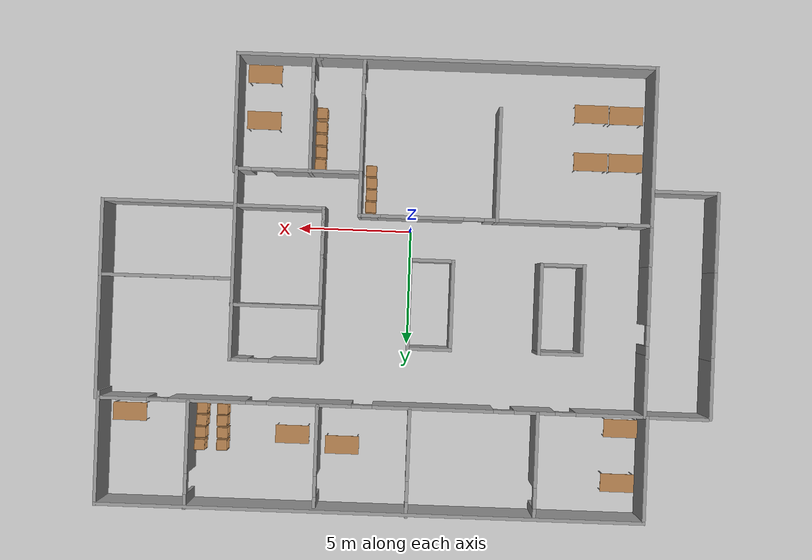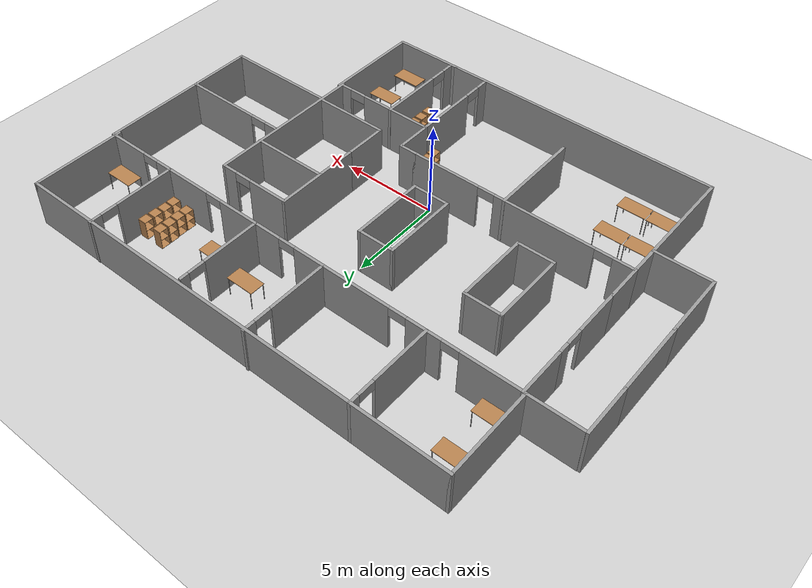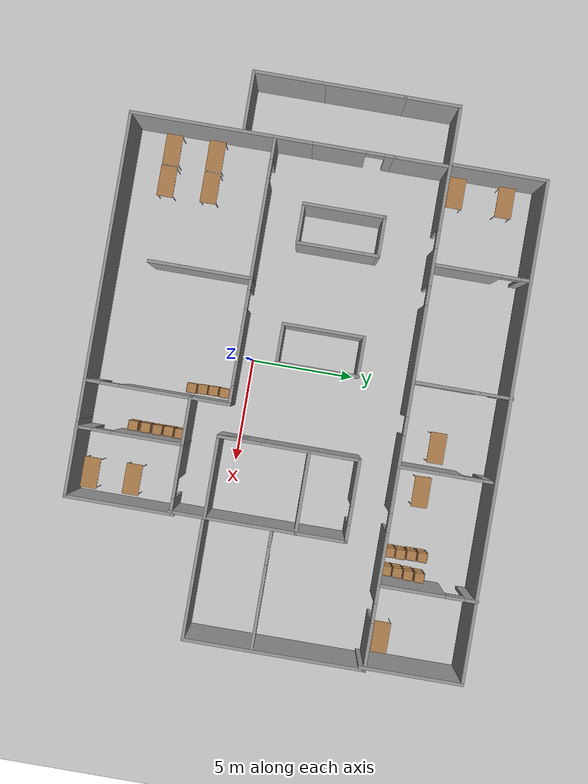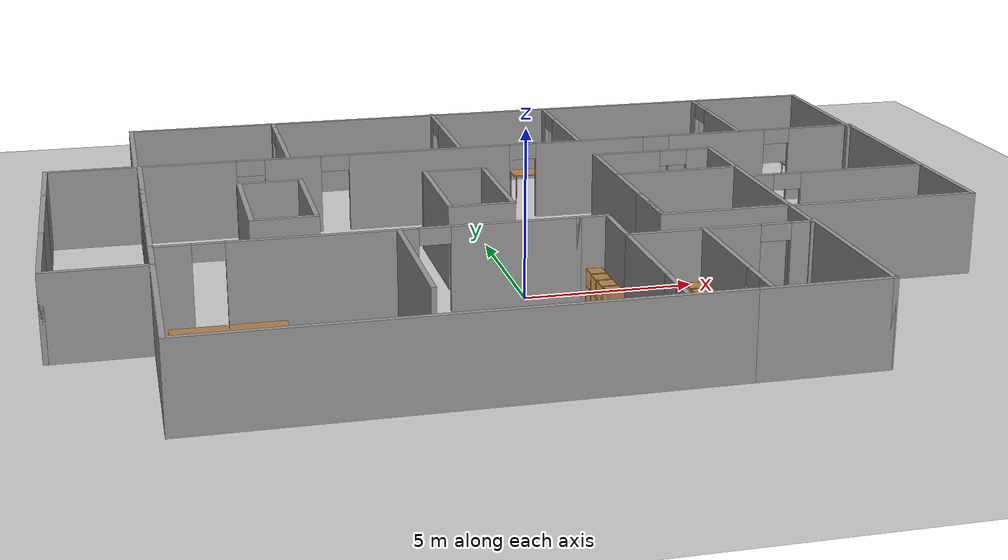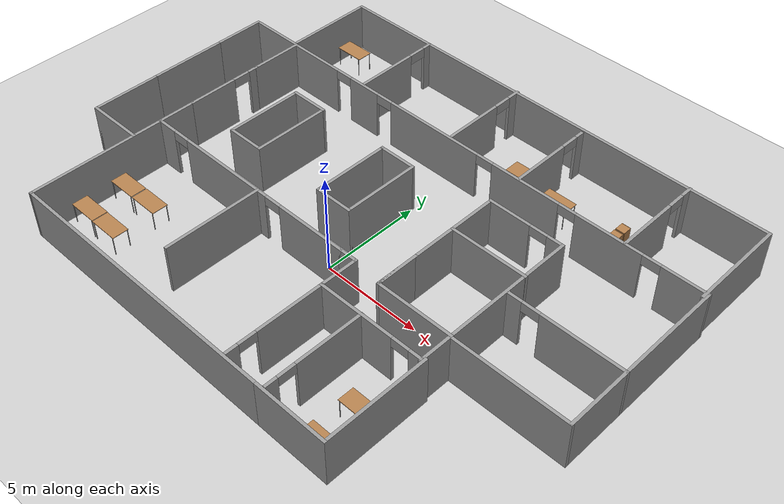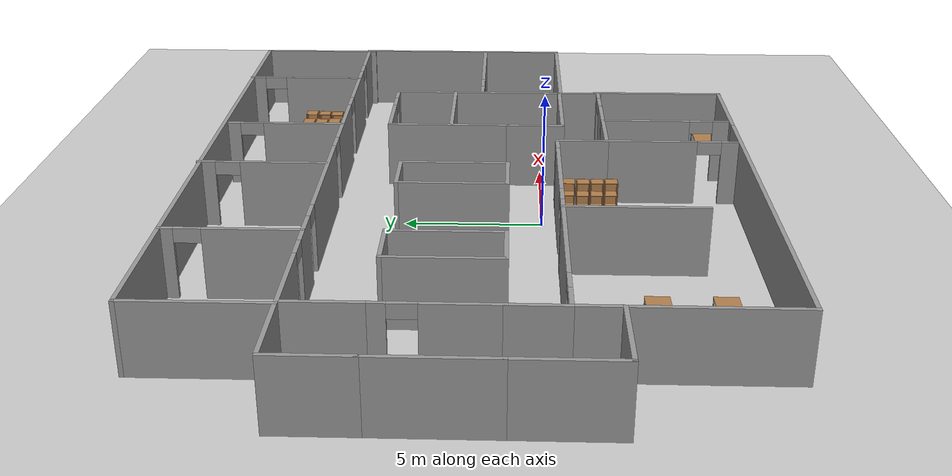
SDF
<sdf version="1.7">
 <world name="default">
  <light name="sun" type="directional">
   <pose>0 0 10 0 -0 0</pose>
   <diffuse>0.8 0.8 0.8 1</diffuse>
   <specular>0.2 0.2 0.2 1</specular>
   <attenuation>
    <range>1000</range>
    <constant>0.9</constant>
    <linear>0.01</linear>
    <quadratic>0.001</quadratic>
   </attenuation>
   <direction>-0.5 0.1 -0.9</direction>
   <spot><inner_angle>0</inner_angle><outer_angle>0</outer_angle><falloff>0</falloff></spot>
  </light>
  <model name="ground_plane">
   <static>1</static>
   <link name="link">
    <collision name="collision">
     <geometry><plane><normal>0 0 1</normal><size>100 100</size></plane></geometry>
     <surface><friction><ode><mu>100</mu><mu2>50</mu2></ode></friction></surface>
    </collision>
    <visual name="visual">
     <cast_shadows>0</cast_shadows>
     <geometry><plane><normal>0 0 1</normal><size>100 100</size></plane></geometry>
     <material>
      <script><uri>file://media/materials/scripts/gazebo.material</uri><name>Gazebo/Grey</name></script>
     </material>
    </visual>
   </link>
  </model>
  <gravity>0 0 -9.8</gravity>
  <magnetic_field>6e-06 2.3e-05 -4.2e-05</magnetic_field>
  <atmosphere type="adiabatic"/>
  <physics name="default_physics" default="0" type="ode">
   <max_step_size>0.001</max_step_size>
   <real_time_factor>1</real_time_factor>
   <real_time_update_rate>1000</real_time_update_rate>
  </physics>
  <scene><ambient>0.4 0.4 0.4 1</ambient><background>0.7 0.7 0.7 1</background><shadows>1</shadows></scene>
  <spherical_coordinates>
   <surface_model>EARTH_WGS84</surface_model>
   <latitude_deg>0</latitude_deg>
   <longitude_deg>0</longitude_deg>
   <elevation>0</elevation>
   <heading_deg>0</heading_deg>
  </spherical_coordinates>
  <model name="voenkomat">
   <pose>0.05123 2.49977 0 0 -0 0</pose>
   <link name="Wall_100">
    <collision name="Wall_100_Collision">
     <geometry><box><size>1 0.15 2.5</size></box></geometry>
     <pose>0 0 1.25 0 -0 0</pose>
    </collision>
    <visual name="Wall_100_Visual">
     <pose>0 0 1.25 0 -0 0</pose>
     <geometry><box><size>1 0.15 2.5</size></box></geometry>
     <material>
      <script><uri>file://media/materials/scripts/gazebo.material</uri><name>Gazebo/Grey</name></script>
      <ambient>1 1 1 1</ambient>
     </material>
     <meta><layer>0</layer></meta>
    </visual>
    <pose>1.77334 -3.06579 0 0 -0 0</pose>
   </link>
   <link name="Wall_103">
    <collision name="Wall_103_Collision">
     <geometry><box><size>2 0.15 2.5</size></box></geometry>
     <pose>0 0 1.25 0 -0 0</pose>
    </collision>
    <visual name="Wall_103_Visual">
     <pose>0 0 1.25 0 -0 0</pose>
     <geometry><box><size>2 0.15 2.5</size></box></geometry>
     <material>
      <script><uri>file://media/materials/scripts/gazebo.material</uri><name>Gazebo/Grey</name></script>
      <ambient>1 1 1 1</ambient>
     </material>
     <meta><layer>0</layer></meta>
    </visual>
    <pose>2.19834 -3.99079 0 0 -0 -1.5708</pose>
   </link>
   <link name="Wall_104">
    <pose>4.87334 -4.91579 0 0 -0 0</pose>
    <visual name="Wall_104_Visual_0">
     <pose>-0.778163 0 1.25 0 -0 0</pose>
     <geometry><box><size>3.94367 0.15 2.5</size></box></geometry>
     <material>
      <script><uri>file://media/materials/scripts/gazebo.material</uri><name>Gazebo/Grey</name></script>
      <ambient>1 1 1 1</ambient>
     </material>
     <meta><layer>0</layer></meta>
    </visual>
    <collision name="Wall_104_Collision_0">
     <geometry><box><size>3.94367 0.15 2.5</size></box></geometry>
     <pose>-0.778163 0 1.25 0 -0 0</pose>
    </collision>
    <visual name="Wall_104_Visual_1">
     <pose>2.42184 0 1.25 0 -0 0</pose>
     <geometry><box><size>0.656325 0.15 2.5</size></box></geometry>
     <material>
      <script><uri>file://media/materials/scripts/gazebo.material</uri><name>Gazebo/Grey</name></script>
      <ambient>1 1 1 1</ambient>
     </material>
     <meta><layer>0</layer></meta>
    </visual>
    <collision name="Wall_104_Collision_1">
     <geometry><box><size>0.656325 0.15 2.5</size></box></geometry>
     <pose>2.42184 0 1.25 0 -0 0</pose>
    </collision>
    <visual name="Wall_104_Visual_2">
     <pose>1.64367 0 2.25 0 -0 0</pose>
     <geometry><box><size>0.9 0.15 0.5</size></box></geometry>
     <material>
      <script><uri>file://media/materials/scripts/gazebo.material</uri><name>Gazebo/Grey</name></script>
      <ambient>1 1 1 1</ambient>
     </material>
     <meta><layer>0</layer></meta>
    </visual>
    <collision name="Wall_104_Collision_2">
     <geometry><box><size>0.9 0.15 0.5</size></box></geometry>
     <pose>1.64367 0 2.25 0 -0 0</pose>
    </collision>
   </link>
   <link name="Wall_106">
    <collision name="Wall_106_Collision">
     <geometry><box><size>8.5 0.15 2.5</size></box></geometry>
     <pose>0 0 1.25 0 -0 0</pose>
    </collision>
    <visual name="Wall_106_Visual">
     <pose>0 0 1.25 0 -0 0</pose>
     <geometry><box><size>8.5 0.15 2.5</size></box></geometry>
     <material>
      <script><uri>file://media/materials/scripts/gazebo.material</uri><name>Gazebo/Grey</name></script>
      <ambient>1 1 1 1</ambient>
     </material>
     <meta><layer>0</layer></meta>
    </visual>
    <pose>7.59834 -0.790787 0 0 -0 -1.5708</pose>
   </link>
   <link name="Wall_116">
    <collision name="Wall_116_Collision">
     <geometry><box><size>3.75 0.15 2.5</size></box></geometry>
     <pose>0 0 1.25 0 -0 0</pose>
    </collision>
    <visual name="Wall_116_Visual">
     <pose>0 0 1.25 0 -0 0</pose>
     <geometry><box><size>3.75 0.15 2.5</size></box></geometry>
     <material>
      <script><uri>file://media/materials/scripts/gazebo.material</uri><name>Gazebo/Grey</name></script>
      <ambient>1 1 1 1</ambient>
     </material>
     <meta><layer>0</layer></meta>
    </visual>
    <pose>5.89834 -9.91579 0 0 -0 0</pose>
   </link>
   <link name="Wall_117">
    <collision name="Wall_117_Collision">
     <geometry><box><size>5.25 0.15 2.5</size></box></geometry>
     <pose>0 0 1.25 0 -0 0</pose>
    </collision>
    <visual name="Wall_117_Visual">
     <pose>0 0 1.25 0 -0 0</pose>
     <geometry><box><size>5.25 0.15 2.5</size></box></geometry>
     <material>
      <script><uri>file://media/materials/scripts/gazebo.material</uri><name>Gazebo/Grey</name></script>
      <ambient>1 1 1 1</ambient>
     </material>
     <meta><layer>0</layer></meta>
    </visual>
    <pose>7.69834 -7.36579 0 0 -0 1.5708</pose>
   </link>
   <link name="Wall_119">
    <collision name="Wall_119_Collision">
     <geometry><box><size>5 0.15 2.5</size></box></geometry>
     <pose>0 0 1.25 0 -0 0</pose>
    </collision>
    <visual name="Wall_119_Visual">
     <pose>0 0 1.25 0 -0 0</pose>
     <geometry><box><size>5 0.15 2.5</size></box></geometry>
     <material>
      <script><uri>file://media/materials/scripts/gazebo.material</uri><name>Gazebo/Grey</name></script>
      <ambient>1 1 1 1</ambient>
     </material>
     <meta><layer>0</layer></meta>
    </visual>
    <pose>-3.78453 -5.48183 0 0 -0 -1.5708</pose>
   </link>
   <link name="Wall_121">
    <pose>2.19834 -7.34079 0 0 -0 -1.5708</pose>
    <visual name="Wall_121_Visual_0">
     <pose>-0.772605 0 1.25 0 -0 0</pose>
     <geometry><box><size>3.45479 0.15 2.5</size></box></geometry>
     <material>
      <script><uri>file://media/materials/scripts/gazebo.material</uri><name>Gazebo/Grey</name></script>
      <ambient>1 1 1 1</ambient>
     </material>
     <meta><layer>0</layer></meta>
    </visual>
    <collision name="Wall_121_Collision_0">
     <geometry><box><size>3.45479 0.15 2.5</size></box></geometry>
     <pose>-0.772605 0 1.25 0 -0 0</pose>
    </collision>
    <visual name="Wall_121_Visual_1">
     <pose>2.1774 0 1.25 0 -0 0</pose>
     <geometry><box><size>0.645211 0.15 2.5</size></box></geometry>
     <material>
      <script><uri>file://media/materials/scripts/gazebo.material</uri><name>Gazebo/Grey</name></script>
      <ambient>1 1 1 1</ambient>
     </material>
     <meta><layer>0</layer></meta>
    </visual>
    <collision name="Wall_121_Collision_1">
     <geometry><box><size>0.645211 0.15 2.5</size></box></geometry>
     <pose>2.1774 0 1.25 0 -0 0</pose>
    </collision>
    <visual name="Wall_121_Visual_2">
     <pose>1.40479 0 2.25 0 -0 0</pose>
     <geometry><box><size>0.9 0.15 0.5</size></box></geometry>
     <material>
      <script><uri>file://media/materials/scripts/gazebo.material</uri><name>Gazebo/Grey</name></script>
      <ambient>1 1 1 1</ambient>
     </material>
     <meta><layer>0</layer></meta>
    </visual>
    <collision name="Wall_121_Collision_2">
     <geometry><box><size>0.9 0.15 0.5</size></box></geometry>
     <pose>1.40479 0 2.25 0 -0 0</pose>
    </collision>
   </link>
   <link name="Wall_126">
    <collision name="Wall_126_Collision">
     <geometry><box><size>8.75 0.15 2.5</size></box></geometry>
     <pose>0 0 1.25 0 -0 0</pose>
    </collision>
    <visual name="Wall_126_Visual">
     <pose>0 0 1.25 0 -0 0</pose>
     <geometry><box><size>8.75 0.15 2.5</size></box></geometry>
     <material>
      <script><uri>file://media/materials/scripts/gazebo.material</uri><name>Gazebo/Grey</name></script>
      <ambient>1 1 1 1</ambient>
     </material>
     <meta><layer>0</layer></meta>
    </visual>
    <pose>13.3483 0.934213 0 0 -0 -1.5708</pose>
   </link>
   <link name="Wall_127">
    <collision name="Wall_127_Collision">
     <geometry><box><size>5.75 0.15 2.5</size></box></geometry>
     <pose>0 0 1.25 0 -0 0</pose>
    </collision>
    <visual name="Wall_127_Visual">
     <pose>0 0 1.25 0 -0 0</pose>
     <geometry><box><size>5.75 0.15 2.5</size></box></geometry>
     <material>
      <script><uri>file://media/materials/scripts/gazebo.material</uri><name>Gazebo/Grey</name></script>
      <ambient>1 1 1 1</ambient>
     </material>
     <meta><layer>0</layer></meta>
    </visual>
    <pose>10.5483 -3.36579 0 0 -0 3.14159</pose>
   </link>
   <link name="Wall_129">
    <pose>10.5517 -0.118334 0 0 -0 3.14159</pose>
    <visual name="Wall_129_Visual_0">
     <pose>-0.809428 0 1.25 0 -0 0</pose>
     <geometry><box><size>4.13114 0.15 2.5</size></box></geometry>
     <material>
      <script><uri>file://media/materials/scripts/gazebo.material</uri><name>Gazebo/Grey</name></script>
      <ambient>1 1 1 1</ambient>
     </material>
     <meta><layer>0</layer></meta>
    </visual>
    <collision name="Wall_129_Collision_0">
     <geometry><box><size>4.13114 0.15 2.5</size></box></geometry>
     <pose>-0.809428 0 1.25 0 -0 0</pose>
    </collision>
    <visual name="Wall_129_Visual_1">
     <pose>2.51557 0 1.25 0 -0 0</pose>
     <geometry><box><size>0.718856 0.15 2.5</size></box></geometry>
     <material>
      <script><uri>file://media/materials/scripts/gazebo.material</uri><name>Gazebo/Grey</name></script>
      <ambient>1 1 1 1</ambient>
     </material>
     <meta><layer>0</layer></meta>
    </visual>
    <collision name="Wall_129_Collision_1">
     <geometry><box><size>0.718856 0.15 2.5</size></box></geometry>
     <pose>2.51557 0 1.25 0 -0 0</pose>
    </collision>
    <visual name="Wall_129_Visual_2">
     <pose>1.70614 0 2.25 0 -0 0</pose>
     <geometry><box><size>0.9 0.15 0.5</size></box></geometry>
     <material>
      <script><uri>file://media/materials/scripts/gazebo.material</uri><name>Gazebo/Grey</name></script>
      <ambient>1 1 1 1</ambient>
     </material>
     <meta><layer>0</layer></meta>
    </visual>
    <collision name="Wall_129_Collision_2">
     <geometry><box><size>0.9 0.15 0.5</size></box></geometry>
     <pose>1.70614 0 2.25 0 -0 0</pose>
    </collision>
   </link>
   <link name="Wall_131">
    <pose>4.41332 -7.33089 0 0 -0 -1.5708</pose>
    <visual name="Wall_131_Visual_0">
     <pose>-0.76586 0 1.25 0 -0 0</pose>
     <geometry><box><size>3.46828 0.15 2.5</size></box></geometry>
     <material>
      <script><uri>file://media/materials/scripts/gazebo.material</uri><name>Gazebo/Grey</name></script>
      <ambient>1 1 1 1</ambient>
     </material>
     <meta><layer>0</layer></meta>
    </visual>
    <collision name="Wall_131_Collision_0">
     <geometry><box><size>3.46828 0.15 2.5</size></box></geometry>
     <pose>-0.76586 0 1.25 0 -0 0</pose>
    </collision>
    <visual name="Wall_131_Visual_1">
     <pose>2.18414 0 1.25 0 -0 0</pose>
     <geometry><box><size>0.63172 0.15 2.5</size></box></geometry>
     <material>
      <script><uri>file://media/materials/scripts/gazebo.material</uri><name>Gazebo/Grey</name></script>
      <ambient>1 1 1 1</ambient>
     </material>
     <meta><layer>0</layer></meta>
    </visual>
    <collision name="Wall_131_Collision_1">
     <geometry><box><size>0.63172 0.15 2.5</size></box></geometry>
     <pose>2.18414 0 1.25 0 -0 0</pose>
    </collision>
    <visual name="Wall_131_Visual_2">
     <pose>1.41828 0 2.25 0 -0 0</pose>
     <geometry><box><size>0.9 0.15 0.5</size></box></geometry>
     <material>
      <script><uri>file://media/materials/scripts/gazebo.material</uri><name>Gazebo/Grey</name></script>
      <ambient>1 1 1 1</ambient>
     </material>
     <meta><layer>0</layer></meta>
    </visual>
    <collision name="Wall_131_Collision_2">
     <geometry><box><size>0.9 0.15 0.5</size></box></geometry>
     <pose>1.41828 0 2.25 0 -0 0</pose>
    </collision>
   </link>
   <link name="Wall_133">
    <collision name="Wall_133_Collision">
     <geometry><box><size>4 0.15 2.5</size></box></geometry>
     <pose>0 0 1.25 0 -0 0</pose>
    </collision>
    <visual name="Wall_133_Visual">
     <pose>0 0 1.25 0 -0 0</pose>
     <geometry><box><size>4 0.15 2.5</size></box></geometry>
     <material>
      <script><uri>file://media/materials/scripts/gazebo.material</uri><name>Gazebo/Grey</name></script>
      <ambient>1 1 1 1</ambient>
     </material>
     <meta><layer>0</layer></meta>
    </visual>
    <pose>5.69103 1.00063 0 0 -0 0</pose>
   </link>
   <link name="Wall_152">
    <pose>3.71917 7.45539 0 0 -0 1.5708</pose>
    <visual name="Wall_152_Visual_0">
     <pose>-0.692996 0 1.25 0 -0 0</pose>
     <geometry><box><size>3.11401 0.15 2.5</size></box></geometry>
     <material>
      <script><uri>file://media/materials/scripts/gazebo.material</uri><name>Gazebo/Grey</name></script>
      <ambient>1 1 1 1</ambient>
     </material>
     <meta><layer>0</layer></meta>
    </visual>
    <collision name="Wall_152_Collision_0">
     <geometry><box><size>3.11401 0.15 2.5</size></box></geometry>
     <pose>-0.692996 0 1.25 0 -0 0</pose>
    </collision>
    <visual name="Wall_152_Visual_1">
     <pose>2.007 0 1.25 0 -0 0</pose>
     <geometry><box><size>0.485991 0.15 2.5</size></box></geometry>
     <material>
      <script><uri>file://media/materials/scripts/gazebo.material</uri><name>Gazebo/Grey</name></script>
      <ambient>1 1 1 1</ambient>
     </material>
     <meta><layer>0</layer></meta>
    </visual>
    <collision name="Wall_152_Collision_1">
     <geometry><box><size>0.485991 0.15 2.5</size></box></geometry>
     <pose>2.007 0 1.25 0 -0 0</pose>
    </collision>
    <visual name="Wall_152_Visual_2">
     <pose>1.31401 0 2.25 0 -0 0</pose>
     <geometry><box><size>0.9 0.15 0.5</size></box></geometry>
     <material>
      <script><uri>file://media/materials/scripts/gazebo.material</uri><name>Gazebo/Grey</name></script>
      <ambient>1 1 1 1</ambient>
     </material>
     <meta><layer>0</layer></meta>
    </visual>
    <collision name="Wall_152_Collision_2">
     <geometry><box><size>0.9 0.15 0.5</size></box></geometry>
     <pose>1.31401 0 2.25 0 -0 0</pose>
    </collision>
   </link>
   <link name="Wall_156">
    <pose>9.33374 7.58039 0 0 -0 1.5708</pose>
    <visual name="Wall_156_Visual_0">
     <pose>-0.77731 0 1.25 0 -0 0</pose>
     <geometry><box><size>3.19538 0.15 2.5</size></box></geometry>
     <material>
      <script><uri>file://media/materials/scripts/gazebo.material</uri><name>Gazebo/Grey</name></script>
      <ambient>1 1 1 1</ambient>
     </material>
     <meta><layer>0</layer></meta>
    </visual>
    <collision name="Wall_156_Collision_0">
     <geometry><box><size>3.19538 0.15 2.5</size></box></geometry>
     <pose>-0.77731 0 1.25 0 -0 0</pose>
    </collision>
    <visual name="Wall_156_Visual_1">
     <pose>2.04769 0 1.25 0 -0 0</pose>
     <geometry><box><size>0.654621 0.15 2.5</size></box></geometry>
     <material>
      <script><uri>file://media/materials/scripts/gazebo.material</uri><name>Gazebo/Grey</name></script>
      <ambient>1 1 1 1</ambient>
     </material>
     <meta><layer>0</layer></meta>
    </visual>
    <collision name="Wall_156_Collision_1">
     <geometry><box><size>0.654621 0.15 2.5</size></box></geometry>
     <pose>2.04769 0 1.25 0 -0 0</pose>
    </collision>
    <visual name="Wall_156_Visual_2">
     <pose>1.27038 0 2.25 0 -0 0</pose>
     <geometry><box><size>0.9 0.15 0.5</size></box></geometry>
     <material>
      <script><uri>file://media/materials/scripts/gazebo.material</uri><name>Gazebo/Grey</name></script>
      <ambient>1 1 1 1</ambient>
     </material>
     <meta><layer>0</layer></meta>
    </visual>
    <collision name="Wall_156_Collision_2">
     <geometry><box><size>0.9 0.15 0.5</size></box></geometry>
     <pose>1.27038 0 2.25 0 -0 0</pose>
    </collision>
   </link>
   <link name="Wall_159">
    <collision name="Wall_159_Collision">
     <geometry><box><size>3.5 0.15 2.5</size></box></geometry>
     <pose>0 0 1.25 0 -0 0</pose>
    </collision>
    <visual name="Wall_159_Visual">
     <pose>0 0 1.25 0 -0 0</pose>
     <geometry><box><size>3.5 0.15 2.5</size></box></geometry>
     <material>
      <script><uri>file://media/materials/scripts/gazebo.material</uri><name>Gazebo/Grey</name></script>
      <ambient>1 1 1 1</ambient>
     </material>
     <meta><layer>0</layer></meta>
    </visual>
    <pose>-13.3517 -2.89079 0 0 -0 -1.5708</pose>
   </link>
   <link name="Wall_162">
    <collision name="Wall_162_Collision">
     <geometry><box><size>3 0.15 2.5</size></box></geometry>
     <pose>0 0 1.25 0 -0 0</pose>
    </collision>
    <visual name="Wall_162_Visual">
     <pose>0 0 1.25 0 -0 0</pose>
     <geometry><box><size>3 0.15 2.5</size></box></geometry>
     <material>
      <script><uri>file://media/materials/scripts/gazebo.material</uri><name>Gazebo/Grey</name></script>
      <ambient>1 1 1 1</ambient>
     </material>
     <meta><layer>0</layer></meta>
    </visual>
    <pose>-11.9267 -4.56579 0 0 -0 0</pose>
   </link>
   <link name="Wall_165">
    <collision name="Wall_165_Collision">
     <geometry><box><size>24 0.15 2.5</size></box></geometry>
     <pose>0 0 1.25 0 -0 0</pose>
    </collision>
    <visual name="Wall_165_Visual">
     <pose>0 0 1.25 0 -0 0</pose>
     <geometry><box><size>24 0.15 2.5</size></box></geometry>
     <material>
      <script><uri>file://media/materials/scripts/gazebo.material</uri><name>Gazebo/Grey</name></script>
      <ambient>1 1 1 1</ambient>
     </material>
     <meta><layer>0</layer></meta>
    </visual>
    <pose>1.31046 9.85172 0 0 -0 0</pose>
   </link>
   <link name="Wall_169">
    <collision name="Wall_169_Collision">
     <geometry><box><size>4.75 0.15 2.5</size></box></geometry>
     <pose>0 0 1.25 0 -0 0</pose>
    </collision>
    <visual name="Wall_169_Visual">
     <pose>0 0 1.25 0 -0 0</pose>
     <geometry><box><size>4.75 0.15 2.5</size></box></geometry>
     <material>
      <script><uri>file://media/materials/scripts/gazebo.material</uri><name>Gazebo/Grey</name></script>
      <ambient>1 1 1 1</ambient>
     </material>
     <meta><layer>0</layer></meta>
    </visual>
    <pose>-10.6145 7.55172 0 0 -0 -1.5708</pose>
   </link>
   <link name="Wall_171">
    <collision name="Wall_171_Collision">
     <geometry><box><size>5 0.15 2.5</size></box></geometry>
     <pose>0 0 1.25 0 -0 0</pose>
    </collision>
    <visual name="Wall_171_Visual">
     <pose>0 0 1.25 0 -0 0</pose>
     <geometry><box><size>5 0.15 2.5</size></box></geometry>
     <material>
      <script><uri>file://media/materials/scripts/gazebo.material</uri><name>Gazebo/Grey</name></script>
      <ambient>1 1 1 1</ambient>
     </material>
     <meta><layer>0</layer></meta>
    </visual>
    <pose>13.2355 7.42672 0 0 -0 -1.5708</pose>
   </link>
   <link name="Wall_176">
    <pose>-5.85231 7.55196 0 0 -0 -1.5708</pose>
    <visual name="Wall_176_Visual_0">
     <pose>-2.10259 0 1.25 0 -0 0</pose>
     <geometry><box><size>0.544819 0.15 2.5</size></box></geometry>
     <material>
      <script><uri>file://media/materials/scripts/gazebo.material</uri><name>Gazebo/Grey</name></script>
      <ambient>1 1 1 1</ambient>
     </material>
     <meta><layer>0</layer></meta>
    </visual>
    <collision name="Wall_176_Collision_0">
     <geometry><box><size>0.544819 0.15 2.5</size></box></geometry>
     <pose>-2.10259 0 1.25 0 -0 0</pose>
    </collision>
    <visual name="Wall_176_Visual_1">
     <pose>0.722409 0 1.25 0 -0 0</pose>
     <geometry><box><size>3.30518 0.15 2.5</size></box></geometry>
     <material>
      <script><uri>file://media/materials/scripts/gazebo.material</uri><name>Gazebo/Grey</name></script>
      <ambient>1 1 1 1</ambient>
     </material>
     <meta><layer>0</layer></meta>
    </visual>
    <collision name="Wall_176_Collision_1">
     <geometry><box><size>3.30518 0.15 2.5</size></box></geometry>
     <pose>0.722409 0 1.25 0 -0 0</pose>
    </collision>
    <visual name="Wall_176_Visual_2">
     <pose>-1.38018 0 2.25 0 -0 0</pose>
     <geometry><box><size>0.9 0.15 0.5</size></box></geometry>
     <material>
      <script><uri>file://media/materials/scripts/gazebo.material</uri><name>Gazebo/Grey</name></script>
      <ambient>1 1 1 1</ambient>
     </material>
     <meta><layer>0</layer></meta>
    </visual>
    <collision name="Wall_176_Collision_2">
     <geometry><box><size>0.9 0.15 0.5</size></box></geometry>
     <pose>-1.38018 0 2.25 0 -0 0</pose>
    </collision>
   </link>
   <link name="Wall_181">
    <pose>-0.289859 7.61579 0 0 -0 -1.5708</pose>
    <visual name="Wall_181_Visual_0">
     <pose>-2.02999 0 1.25 0 -0 0</pose>
     <geometry><box><size>0.690014 0.15 2.5</size></box></geometry>
     <material>
      <script><uri>file://media/materials/scripts/gazebo.material</uri><name>Gazebo/Grey</name></script>
      <ambient>1 1 1 1</ambient>
     </material>
     <meta><layer>0</layer></meta>
    </visual>
    <collision name="Wall_181_Collision_0">
     <geometry><box><size>0.690014 0.15 2.5</size></box></geometry>
     <pose>-2.02999 0 1.25 0 -0 0</pose>
    </collision>
    <visual name="Wall_181_Visual_1">
     <pose>0.795007 0 1.25 0 -0 0</pose>
     <geometry><box><size>3.15999 0.15 2.5</size></box></geometry>
     <material>
      <script><uri>file://media/materials/scripts/gazebo.material</uri><name>Gazebo/Grey</name></script>
      <ambient>1 1 1 1</ambient>
     </material>
     <meta><layer>0</layer></meta>
    </visual>
    <collision name="Wall_181_Collision_1">
     <geometry><box><size>3.15999 0.15 2.5</size></box></geometry>
     <pose>0.795007 0 1.25 0 -0 0</pose>
    </collision>
    <visual name="Wall_181_Visual_2">
     <pose>-1.23499 0 2.25 0 -0 0</pose>
     <geometry><box><size>0.9 0.15 0.5</size></box></geometry>
     <material>
      <script><uri>file://media/materials/scripts/gazebo.material</uri><name>Gazebo/Grey</name></script>
      <ambient>1 1 1 1</ambient>
     </material>
     <meta><layer>0</layer></meta>
    </visual>
    <collision name="Wall_181_Collision_2">
     <geometry><box><size>0.9 0.15 0.5</size></box></geometry>
     <pose>-1.23499 0 2.25 0 -0 0</pose>
    </collision>
   </link>
   <link name="Wall_183">
    <collision name="Wall_183_Collision">
     <geometry><box><size>2.75 0.15 2.5</size></box></geometry>
     <pose>0 0 1.25 0 -0 0</pose>
    </collision>
    <visual name="Wall_183_Visual">
     <pose>0 0 1.25 0 -0 0</pose>
     <geometry><box><size>2.75 0.15 2.5</size></box></geometry>
     <material>
      <script><uri>file://media/materials/scripts/gazebo.material</uri><name>Gazebo/Grey</name></script>
      <ambient>1 1 1 1</ambient>
     </material>
     <meta><layer>0</layer></meta>
    </visual>
    <pose>-11.9145 5.25172 0 0 -0 3.14159</pose>
   </link>
   <link name="Wall_185">
    <collision name="Wall_185_Collision">
     <geometry><box><size>2.75 0.15 2.5</size></box></geometry>
     <pose>0 0 1.25 0 -0 0</pose>
    </collision>
    <visual name="Wall_185_Visual">
     <pose>0 0 1.25 0 -0 0</pose>
     <geometry><box><size>2.75 0.15 2.5</size></box></geometry>
     <material>
      <script><uri>file://media/materials/scripts/gazebo.material</uri><name>Gazebo/Grey</name></script>
      <ambient>1 1 1 1</ambient>
     </material>
     <meta><layer>0</layer></meta>
    </visual>
    <pose>-13.3517 3.93421 0 0 -0 1.5708</pose>
   </link>
   <link name="Wall_25">
    <collision name="Wall_25_Collision">
     <geometry><box><size>4 0.15 2.5</size></box></geometry>
     <pose>0 0 1.25 0 -0 0</pose>
    </collision>
    <visual name="Wall_25_Visual">
     <pose>0 0 1.25 0 -0 0</pose>
     <geometry><box><size>4 0.15 2.5</size></box></geometry>
     <material>
      <script><uri>file://media/materials/scripts/gazebo.material</uri><name>Gazebo/Grey</name></script>
      <ambient>1 1 1 1</ambient>
     </material>
     <meta><layer>0</layer></meta>
    </visual>
    <pose>-0.101664 0.709213 0 0 -0 1.5708</pose>
   </link>
   <link name="Wall_26">
    <collision name="Wall_26_Collision">
     <geometry><box><size>2 0.15 2.5</size></box></geometry>
     <pose>0 0 1.25 0 -0 0</pose>
    </collision>
    <visual name="Wall_26_Visual">
     <pose>0 0 1.25 0 -0 0</pose>
     <geometry><box><size>2 0.15 2.5</size></box></geometry>
     <material>
      <script><uri>file://media/materials/scripts/gazebo.material</uri><name>Gazebo/Grey</name></script>
      <ambient>1 1 1 1</ambient>
     </material>
     <meta><layer>0</layer></meta>
    </visual>
    <pose>-1.02666 2.63421 0 0 -0 3.14159</pose>
   </link>
   <link name="Wall_27">
    <collision name="Wall_27_Collision">
     <geometry><box><size>4 0.15 2.5</size></box></geometry>
     <pose>0 0 1.25 0 -0 0</pose>
    </collision>
    <visual name="Wall_27_Visual">
     <pose>0 0 1.25 0 -0 0</pose>
     <geometry><box><size>4 0.15 2.5</size></box></geometry>
     <material>
      <script><uri>file://media/materials/scripts/gazebo.material</uri><name>Gazebo/Grey</name></script>
      <ambient>1 1 1 1</ambient>
     </material>
     <meta><layer>0</layer></meta>
    </visual>
    <pose>-1.95166 0.709213 0 0 -0 -1.5708</pose>
   </link>
   <link name="Wall_28">
    <collision name="Wall_28_Collision">
     <geometry><box><size>2 0.15 2.5</size></box></geometry>
     <pose>0 0 1.25 0 -0 0</pose>
    </collision>
    <visual name="Wall_28_Visual">
     <pose>0 0 1.25 0 -0 0</pose>
     <geometry><box><size>2 0.15 2.5</size></box></geometry>
     <material>
      <script><uri>file://media/materials/scripts/gazebo.material</uri><name>Gazebo/Grey</name></script>
      <ambient>1 1 1 1</ambient>
     </material>
     <meta><layer>0</layer></meta>
    </visual>
    <pose>-1.02666 -1.21579 0 0 -0 0</pose>
   </link>
   <link name="Wall_31">
    <collision name="Wall_31_Collision">
     <geometry><box><size>4 0.15 2.5</size></box></geometry>
     <pose>0 0 1.25 0 -0 0</pose>
    </collision>
    <visual name="Wall_31_Visual">
     <pose>0 0 1.25 0 -0 0</pose>
     <geometry><box><size>4 0.15 2.5</size></box></geometry>
     <material>
      <script><uri>file://media/materials/scripts/gazebo.material</uri><name>Gazebo/Grey</name></script>
      <ambient>1 1 1 1</ambient>
     </material>
     <meta><layer>0</layer></meta>
    </visual>
    <pose>-5.80166 0.709213 0 0 -0 1.5708</pose>
   </link>
   <link name="Wall_36">
    <collision name="Wall_36_Collision">
     <geometry><box><size>2 0.15 2.5</size></box></geometry>
     <pose>0 0 1.25 0 -0 0</pose>
    </collision>
    <visual name="Wall_36_Visual">
     <pose>0 0 1.25 0 -0 0</pose>
     <geometry><box><size>2 0.15 2.5</size></box></geometry>
     <material>
      <script><uri>file://media/materials/scripts/gazebo.material</uri><name>Gazebo/Grey</name></script>
      <ambient>1 1 1 1</ambient>
     </material>
     <meta><layer>0</layer></meta>
    </visual>
    <pose>-6.72666 2.63421 0 0 -0 3.14159</pose>
   </link>
   <link name="Wall_37">
    <collision name="Wall_37_Collision">
     <geometry><box><size>4 0.15 2.5</size></box></geometry>
     <pose>0 0 1.25 0 -0 0</pose>
    </collision>
    <visual name="Wall_37_Visual">
     <pose>0 0 1.25 0 -0 0</pose>
     <geometry><box><size>4 0.15 2.5</size></box></geometry>
     <material>
      <script><uri>file://media/materials/scripts/gazebo.material</uri><name>Gazebo/Grey</name></script>
      <ambient>1 1 1 1</ambient>
     </material>
     <meta><layer>0</layer></meta>
    </visual>
    <pose>-7.65166 0.709213 0 0 -0 -1.5708</pose>
   </link>
   <link name="Wall_38">
    <collision name="Wall_38_Collision">
     <geometry><box><size>2 0.15 2.5</size></box></geometry>
     <pose>0 0 1.25 0 -0 0</pose>
    </collision>
    <visual name="Wall_38_Visual">
     <pose>0 0 1.25 0 -0 0</pose>
     <geometry><box><size>2 0.15 2.5</size></box></geometry>
     <material>
      <script><uri>file://media/materials/scripts/gazebo.material</uri><name>Gazebo/Grey</name></script>
      <ambient>1 1 1 1</ambient>
     </material>
     <meta><layer>0</layer></meta>
    </visual>
    <pose>-6.72666 -1.21579 0 0 -0 0</pose>
   </link>
   <link name="Wall_41">
    <pose>-10.5017 0.709213 0 0 -0 1.5708</pose>
    <visual name="Wall_41_Visual_0">
     <pose>-0.729563 0 1.25 0 -0 0</pose>
     <geometry><box><size>2.54087 0.15 2.5</size></box></geometry>
     <material>
      <script><uri>file://media/materials/scripts/gazebo.material</uri><name>Gazebo/Grey</name></script>
      <ambient>1 1 1 1</ambient>
     </material>
     <meta><layer>0</layer></meta>
    </visual>
    <collision name="Wall_41_Collision_0">
     <geometry><box><size>2.54087 0.15 2.5</size></box></geometry>
     <pose>-0.729563 0 1.25 0 -0 0</pose>
    </collision>
    <visual name="Wall_41_Visual_1">
     <pose>1.72044 0 1.25 0 -0 0</pose>
     <geometry><box><size>0.559126 0.15 2.5</size></box></geometry>
     <material>
      <script><uri>file://media/materials/scripts/gazebo.material</uri><name>Gazebo/Grey</name></script>
      <ambient>1 1 1 1</ambient>
     </material>
     <meta><layer>0</layer></meta>
    </visual>
    <collision name="Wall_41_Collision_1">
     <geometry><box><size>0.559126 0.15 2.5</size></box></geometry>
     <pose>1.72044 0 1.25 0 -0 0</pose>
    </collision>
    <visual name="Wall_41_Visual_2">
     <pose>0.990874 0 2.25 0 -0 0</pose>
     <geometry><box><size>0.9 0.15 0.5</size></box></geometry>
     <material>
      <script><uri>file://media/materials/scripts/gazebo.material</uri><name>Gazebo/Grey</name></script>
      <ambient>1 1 1 1</ambient>
     </material>
     <meta><layer>0</layer></meta>
    </visual>
    <collision name="Wall_41_Collision_2">
     <geometry><box><size>0.9 0.15 0.5</size></box></geometry>
     <pose>0.990874 0 2.25 0 -0 0</pose>
    </collision>
   </link>
   <link name="Wall_49">
    <collision name="Wall_49_Collision">
     <geometry><box><size>4 0.15 2.5</size></box></geometry>
     <pose>0 0 1.25 0 -0 0</pose>
    </collision>
    <visual name="Wall_49_Visual">
     <pose>0 0 1.25 0 -0 0</pose>
     <geometry><box><size>4 0.15 2.5</size></box></geometry>
     <material>
      <script><uri>file://media/materials/scripts/gazebo.material</uri><name>Gazebo/Grey</name></script>
      <ambient>1 1 1 1</ambient>
     </material>
     <meta><layer>0</layer></meta>
    </visual>
    <pose>-13.3517 0.709213 0 0 -0 -1.5708</pose>
   </link>
   <link name="Wall_52">
    <collision name="Wall_52_Collision">
     <geometry><box><size>2 0.15 2.5</size></box></geometry>
     <pose>0 0 1.25 0 -0 0</pose>
    </collision>
    <visual name="Wall_52_Visual">
     <pose>0 0 1.25 0 -0 0</pose>
     <geometry><box><size>2 0.15 2.5</size></box></geometry>
     <material>
      <script><uri>file://media/materials/scripts/gazebo.material</uri><name>Gazebo/Grey</name></script>
      <ambient>1 1 1 1</ambient>
     </material>
     <meta><layer>0</layer></meta>
    </visual>
    <pose>-10.5017 -2.14079 0 0 -0 -1.5708</pose>
   </link>
   <link name="Wall_53">
    <pose>-4.57666 -3.06579 0 0 -0 0</pose>
    <visual name="Wall_53_Visual_0">
     <pose>-5.42324 0 1.25 0 -0 0</pose>
     <geometry><box><size>1.15352 0.15 2.5</size></box></geometry>
     <material>
      <script><uri>file://media/materials/scripts/gazebo.material</uri><name>Gazebo/Grey</name></script>
      <ambient>1 1 1 1</ambient>
     </material>
     <meta><layer>0</layer></meta>
    </visual>
    <collision name="Wall_53_Collision_0">
     <geometry><box><size>1.15352 0.15 2.5</size></box></geometry>
     <pose>-5.42324 0 1.25 0 -0 0</pose>
    </collision>
    <visual name="Wall_53_Visual_1">
     <pose>-1.3038 0 1.25 0 -0 0</pose>
     <geometry><box><size>5.28537 0.15 2.5</size></box></geometry>
     <material>
      <script><uri>file://media/materials/scripts/gazebo.material</uri><name>Gazebo/Grey</name></script>
      <ambient>1 1 1 1</ambient>
     </material>
     <meta><layer>0</layer></meta>
    </visual>
    <collision name="Wall_53_Collision_1">
     <geometry><box><size>5.28537 0.15 2.5</size></box></geometry>
     <pose>-1.3038 0 1.25 0 -0 0</pose>
    </collision>
    <visual name="Wall_53_Visual_2">
     <pose>4.11945 0 1.25 0 -0 0</pose>
     <geometry><box><size>3.76111 0.15 2.5</size></box></geometry>
     <material>
      <script><uri>file://media/materials/scripts/gazebo.material</uri><name>Gazebo/Grey</name></script>
      <ambient>1 1 1 1</ambient>
     </material>
     <meta><layer>0</layer></meta>
    </visual>
    <collision name="Wall_53_Collision_2">
     <geometry><box><size>3.76111 0.15 2.5</size></box></geometry>
     <pose>4.11945 0 1.25 0 -0 0</pose>
    </collision>
    <visual name="Wall_53_Visual_3">
     <pose>-4.39648 0 2.25 0 -0 0</pose>
     <geometry><box><size>0.9 0.15 0.5</size></box></geometry>
     <material>
      <script><uri>file://media/materials/scripts/gazebo.material</uri><name>Gazebo/Grey</name></script>
      <ambient>1 1 1 1</ambient>
     </material>
     <meta><layer>0</layer></meta>
    </visual>
    <collision name="Wall_53_Collision_3">
     <geometry><box><size>0.9 0.15 0.5</size></box></geometry>
     <pose>-4.39648 0 2.25 0 -0 0</pose>
    </collision>
    <visual name="Wall_53_Visual_4">
     <pose>1.78889 0 2.25 0 -0 0</pose>
     <geometry><box><size>0.9 0.15 0.5</size></box></geometry>
     <material>
      <script><uri>file://media/materials/scripts/gazebo.material</uri><name>Gazebo/Grey</name></script>
      <ambient>1 1 1 1</ambient>
     </material>
     <meta><layer>0</layer></meta>
    </visual>
    <collision name="Wall_53_Collision_4">
     <geometry><box><size>0.9 0.15 0.5</size></box></geometry>
     <pose>1.78889 0 2.25 0 -0 0</pose>
    </collision>
   </link>
   <link name="Wall_56">
    <collision name="Wall_56_Collision">
     <geometry><box><size>4.75 0.15 2.5</size></box></geometry>
     <pose>0 0 1.25 0 -0 0</pose>
    </collision>
    <visual name="Wall_56_Visual">
     <pose>0 0 1.25 0 -0 0</pose>
     <geometry><box><size>4.75 0.15 2.5</size></box></geometry>
     <material>
      <script><uri>file://media/materials/scripts/gazebo.material</uri><name>Gazebo/Grey</name></script>
      <ambient>1 1 1 1</ambient>
     </material>
     <meta><layer>0</layer></meta>
    </visual>
    <pose>3.74834 1.08421 0 0 -0 1.5708</pose>
   </link>
   <link name="Wall_57">
    <pose>5.67334 3.38421 0 0 -0 0</pose>
    <visual name="Wall_57_Visual_0">
     <pose>-0.884074 0 1.25 0 -0 0</pose>
     <geometry><box><size>2.23185 0.15 2.5</size></box></geometry>
     <material>
      <script><uri>file://media/materials/scripts/gazebo.material</uri><name>Gazebo/Grey</name></script>
      <ambient>1 1 1 1</ambient>
     </material>
     <meta><layer>0</layer></meta>
    </visual>
    <collision name="Wall_57_Collision_0">
     <geometry><box><size>2.23185 0.15 2.5</size></box></geometry>
     <pose>-0.884074 0 1.25 0 -0 0</pose>
    </collision>
    <visual name="Wall_57_Visual_1">
     <pose>1.56593 0 1.25 0 -0 0</pose>
     <geometry><box><size>0.868148 0.15 2.5</size></box></geometry>
     <material>
      <script><uri>file://media/materials/scripts/gazebo.material</uri><name>Gazebo/Grey</name></script>
      <ambient>1 1 1 1</ambient>
     </material>
     <meta><layer>0</layer></meta>
    </visual>
    <collision name="Wall_57_Collision_1">
     <geometry><box><size>0.868148 0.15 2.5</size></box></geometry>
     <pose>1.56593 0 1.25 0 -0 0</pose>
    </collision>
    <visual name="Wall_57_Visual_2">
     <pose>0.681852 0 2.25 0 -0 0</pose>
     <geometry><box><size>0.9 0.15 0.5</size></box></geometry>
     <material>
      <script><uri>file://media/materials/scripts/gazebo.material</uri><name>Gazebo/Grey</name></script>
      <ambient>1 1 1 1</ambient>
     </material>
     <meta><layer>0</layer></meta>
    </visual>
    <collision name="Wall_57_Collision_2">
     <geometry><box><size>0.9 0.15 0.5</size></box></geometry>
     <pose>0.681852 0 2.25 0 -0 0</pose>
    </collision>
   </link>
   <link name="Wall_60">
    <collision name="Wall_60_Collision">
     <geometry><box><size>7 0.15 2.5</size></box></geometry>
     <pose>0 0 1.25 0 -0 0</pose>
    </collision>
    <visual name="Wall_60_Visual">
     <pose>0 0 1.25 0 -0 0</pose>
     <geometry><box><size>7 0.15 2.5</size></box></geometry>
     <material>
      <script><uri>file://media/materials/scripts/gazebo.material</uri><name>Gazebo/Grey</name></script>
      <ambient>1 1 1 1</ambient>
     </material>
     <meta><layer>0</layer></meta>
    </visual>
    <pose>-10.5017 -6.49079 0 0 -0 -1.5708</pose>
   </link>
   <link name="Wall_61">
    <collision name="Wall_61_Collision">
     <geometry><box><size>14.75 0.15 2.5</size></box></geometry>
     <pose>0 0 1.25 0 -0 0</pose>
    </collision>
    <visual name="Wall_61_Visual">
     <pose>0 0 1.25 0 -0 0</pose>
     <geometry><box><size>14.75 0.15 2.5</size></box></geometry>
     <material>
      <script><uri>file://media/materials/scripts/gazebo.material</uri><name>Gazebo/Grey</name></script>
      <ambient>1 1 1 1</ambient>
     </material>
     <meta><layer>0</layer></meta>
    </visual>
    <pose>-3.20166 -9.91579 0 0 -0 0</pose>
   </link>
   <link name="Wall_69">
    <collision name="Wall_69_Collision">
     <geometry><box><size>2.75 0.15 2.5</size></box></geometry>
     <pose>0 0 1.25 0 -0 0</pose>
    </collision>
    <visual name="Wall_69_Visual">
     <pose>0 0 1.25 0 -0 0</pose>
     <geometry><box><size>2.75 0.15 2.5</size></box></geometry>
     <material>
      <script><uri>file://media/materials/scripts/gazebo.material</uri><name>Gazebo/Grey</name></script>
      <ambient>1 1 1 1</ambient>
     </material>
     <meta><layer>0</layer></meta>
    </visual>
    <pose>-10.5017 3.93421 0 0 -0 1.5708</pose>
   </link>
   <link name="Wall_70">
    <pose>1.42334 5.23421 0 0 -0 0</pose>
    <visual name="Wall_70_Visual_0">
     <pose>-10.4694 0 1.25 0 -0 0</pose>
     <geometry><box><size>3.06121 0.15 2.5</size></box></geometry>
     <material>
      <script><uri>file://media/materials/scripts/gazebo.material</uri><name>Gazebo/Grey</name></script>
      <ambient>1 1 1 1</ambient>
     </material>
     <meta><layer>0</layer></meta>
    </visual>
    <collision name="Wall_70_Collision_0">
     <geometry><box><size>3.06121 0.15 2.5</size></box></geometry>
     <pose>-10.4694 0 1.25 0 -0 0</pose>
    </collision>
    <visual name="Wall_70_Visual_1">
     <pose>-7.14617 0 1.25 0 -0 0</pose>
     <geometry><box><size>1.78523 0.15 2.5</size></box></geometry>
     <material>
      <script><uri>file://media/materials/scripts/gazebo.material</uri><name>Gazebo/Grey</name></script>
      <ambient>1 1 1 1</ambient>
     </material>
     <meta><layer>0</layer></meta>
    </visual>
    <collision name="Wall_70_Collision_1">
     <geometry><box><size>1.78523 0.15 2.5</size></box></geometry>
     <pose>-7.14617 0 1.25 0 -0 0</pose>
    </collision>
    <visual name="Wall_70_Visual_2">
     <pose>-2.71147 0 1.25 0 -0 0</pose>
     <geometry><box><size>5.28417 0.15 2.5</size></box></geometry>
     <material>
      <script><uri>file://media/materials/scripts/gazebo.material</uri><name>Gazebo/Grey</name></script>
      <ambient>1 1 1 1</ambient>
     </material>
     <meta><layer>0</layer></meta>
    </visual>
    <collision name="Wall_70_Collision_2">
     <geometry><box><size>5.28417 0.15 2.5</size></box></geometry>
     <pose>-2.71147 0 1.25 0 -0 0</pose>
    </collision>
    <visual name="Wall_70_Visual_3">
     <pose>2.66757 0 1.25 0 -0 0</pose>
     <geometry><box><size>3.67391 0.15 2.5</size></box></geometry>
     <material>
      <script><uri>file://media/materials/scripts/gazebo.material</uri><name>Gazebo/Grey</name></script>
      <ambient>1 1 1 1</ambient>
     </material>
     <meta><layer>0</layer></meta>
    </visual>
    <collision name="Wall_70_Collision_3">
     <geometry><box><size>3.67391 0.15 2.5</size></box></geometry>
     <pose>2.66757 0 1.25 0 -0 0</pose>
    </collision>
    <visual name="Wall_70_Visual_4">
     <pose>7.10227 0 1.25 0 -0 0</pose>
     <geometry><box><size>3.39549 0.15 2.5</size></box></geometry>
     <material>
      <script><uri>file://media/materials/scripts/gazebo.material</uri><name>Gazebo/Grey</name></script>
      <ambient>1 1 1 1</ambient>
     </material>
     <meta><layer>0</layer></meta>
    </visual>
    <collision name="Wall_70_Collision_4">
     <geometry><box><size>3.39549 0.15 2.5</size></box></geometry>
     <pose>7.10227 0 1.25 0 -0 0</pose>
    </collision>
    <visual name="Wall_70_Visual_5">
     <pose>10.85 0 1.25 0 -0 0</pose>
     <geometry><box><size>2.29999 0.15 2.5</size></box></geometry>
     <material>
      <script><uri>file://media/materials/scripts/gazebo.material</uri><name>Gazebo/Grey</name></script>
      <ambient>1 1 1 1</ambient>
     </material>
     <meta><layer>0</layer></meta>
    </visual>
    <collision name="Wall_70_Collision_5">
     <geometry><box><size>2.29999 0.15 2.5</size></box></geometry>
     <pose>10.85 0 1.25 0 -0 0</pose>
    </collision>
    <visual name="Wall_70_Visual_6">
     <pose>-8.48879 0 2.25 0 -0 0</pose>
     <geometry><box><size>0.9 0.15 0.5</size></box></geometry>
     <material>
      <script><uri>file://media/materials/scripts/gazebo.material</uri><name>Gazebo/Grey</name></script>
      <ambient>1 1 1 1</ambient>
     </material>
     <meta><layer>0</layer></meta>
    </visual>
    <collision name="Wall_70_Collision_6">
     <geometry><box><size>0.9 0.15 0.5</size></box></geometry>
     <pose>-8.48879 0 2.25 0 -0 0</pose>
    </collision>
    <visual name="Wall_70_Visual_7">
     <pose>-5.80356 0 2.25 0 -0 0</pose>
     <geometry><box><size>0.9 0.15 0.5</size></box></geometry>
     <material>
      <script><uri>file://media/materials/scripts/gazebo.material</uri><name>Gazebo/Grey</name></script>
      <ambient>1 1 1 1</ambient>
     </material>
     <meta><layer>0</layer></meta>
    </visual>
    <collision name="Wall_70_Collision_7">
     <geometry><box><size>0.9 0.15 0.5</size></box></geometry>
     <pose>-5.80356 0 2.25 0 -0 0</pose>
    </collision>
    <visual name="Wall_70_Visual_8">
     <pose>0.380612 0 2.25 0 -0 0</pose>
     <geometry><box><size>0.9 0.15 0.5</size></box></geometry>
     <material>
      <script><uri>file://media/materials/scripts/gazebo.material</uri><name>Gazebo/Grey</name></script>
      <ambient>1 1 1 1</ambient>
     </material>
     <meta><layer>0</layer></meta>
    </visual>
    <collision name="Wall_70_Collision_8">
     <geometry><box><size>0.9 0.15 0.5</size></box></geometry>
     <pose>0.380612 0 2.25 0 -0 0</pose>
    </collision>
    <visual name="Wall_70_Visual_9">
     <pose>4.95452 0 2.25 0 -0 0</pose>
     <geometry><box><size>0.9 0.15 0.5</size></box></geometry>
     <material>
      <script><uri>file://media/materials/scripts/gazebo.material</uri><name>Gazebo/Grey</name></script>
      <ambient>1 1 1 1</ambient>
     </material>
     <meta><layer>0</layer></meta>
    </visual>
    <collision name="Wall_70_Collision_9">
     <geometry><box><size>0.9 0.15 0.5</size></box></geometry>
     <pose>4.95452 0 2.25 0 -0 0</pose>
    </collision>
    <visual name="Wall_70_Visual_10">
     <pose>9.25001 0 2.25 0 -0 0</pose>
     <geometry><box><size>0.9 0.15 0.5</size></box></geometry>
     <material>
      <script><uri>file://media/materials/scripts/gazebo.material</uri><name>Gazebo/Grey</name></script>
      <ambient>1 1 1 1</ambient>
     </material>
     <meta><layer>0</layer></meta>
    </visual>
    <collision name="Wall_70_Collision_10">
     <geometry><box><size>0.9 0.15 0.5</size></box></geometry>
     <pose>9.25001 0 2.25 0 -0 0</pose>
    </collision>
   </link>
   <link name="Wall_96">
    <pose>3.74834 -2.26579 0 0 -0 -1.5708</pose>
    <visual name="Wall_96_Visual_0">
     <pose>0 0 1.25 0 -0 0</pose>
     <geometry><box><size>2.25 0.15 2.5</size></box></geometry>
     <material>
      <script><uri>file://media/materials/scripts/gazebo.material</uri><name>Gazebo/Grey</name></script>
      <ambient>1 1 1 1</ambient>
     </material>
     <meta><layer>0</layer></meta>
    </visual>
    <collision name="Wall_96_Collision_0">
     <geometry><box><size>2.25 0.15 2.5</size></box></geometry>
     <pose>0 0 1.25 0 -0 0</pose>
    </collision>
    <visual name="Wall_96_Visual_1">
     <pose>0.428645 0 1.25 0 -0 0</pose>
     <geometry><box><size>1.39271 0.15 2.5</size></box></geometry>
     <material>
      <script><uri>file://media/materials/scripts/gazebo.material</uri><name>Gazebo/Grey</name></script>
      <ambient>1 1 1 1</ambient>
     </material>
     <meta><layer>0</layer></meta>
    </visual>
    <collision name="Wall_96_Collision_1">
     <geometry><box><size>1.39271 0.15 2.5</size></box></geometry>
     <pose>0.428645 0 1.25 0 -0 0</pose>
    </collision>
   </link>
   <link name="Wall_97">
    <collision name="Wall_97_Collision">
     <geometry><box><size>4 0.15 2.5</size></box></geometry>
     <pose>0 0 1.25 0 -0 0</pose>
    </collision>
    <visual name="Wall_97_Visual">
     <pose>0 0 1.25 0 -0 0</pose>
     <geometry><box><size>4 0.15 2.5</size></box></geometry>
     <material>
      <script><uri>file://media/materials/scripts/gazebo.material</uri><name>Gazebo/Grey</name></script>
      <ambient>1 1 1 1</ambient>
     </material>
     <meta><layer>0</layer></meta>
    </visual>
    <pose>5.67334 -3.31579 0 0 -0 0</pose>
   </link>
   <static>1</static>
  </model>
  <model name="cabinet">
   <static>1</static>
   <link name="cabinet_bottom_plate">
    <inertial>
     <pose>0 0 -1 0 -0 0</pose>
     <inertia><ixx>2.05</ixx><ixy>0</ixy><ixz>0</ixz><iyy>2.05</iyy><iyz>0</iyz><izz>2.05</izz></inertia>
     <mass>25</mass>
    </inertial>
    <collision name="cabinet_bottom_plate_geom">
     <pose>0 0 0.01 0 -0 0</pose>
     <geometry><box><size>0.45 0.45 0.02</size></box></geometry>
    </collision>
    <visual name="cabinet_bottom_plate_geom_visual">
     <pose>0 0 0.01 0 -0 0</pose>
     <geometry><box><size>0.45 0.45 0.02</size></box></geometry>
     <material>
      <script><uri>file://media/materials/scripts/gazebo.material</uri><name>Gazebo/Wood</name></script>
     </material>
    </visual>
    <collision name="cabinet_bottom_plate_geom_cabinet_back_plate">
     <pose>0.235 0 0.51 0 -0 0</pose>
     <geometry><box><size>0.02 0.45 1.02</size></box></geometry>
    </collision>
    <visual name="cabinet_bottom_plate_geom_cabinet_back_plate_visual">
     <pose>0.235 0 0.51 0 -0 0</pose>
     <geometry><box><size>0.02 0.45 1.02</size></box></geometry>
     <material>
      <script><uri>file://media/materials/scripts/gazebo.material</uri><name>Gazebo/Wood</name></script>
     </material>
    </visual>
    <collision name="cabinet_bottom_plate_geom_cabinet_left_plate">
     <pose>0 0.235 0.51 0 -0 0</pose>
     <geometry><box><size>0.45 0.02 1.02</size></box></geometry>
    </collision>
    <visual name="cabinet_bottom_plate_geom_cabinet_left_plate_visual">
     <pose>0 0.235 0.51 0 -0 0</pose>
     <geometry><box><size>0.45 0.02 1.02</size></box></geometry>
     <material>
      <script><uri>file://media/materials/scripts/gazebo.material</uri><name>Gazebo/Wood</name></script>
     </material>
    </visual>
    <collision name="cabinet_bottom_plate_geom_cabinet_middle_plate">
     <pose>0 0 0.51 0 -0 0</pose>
     <geometry><box><size>0.45 0.45 0.02</size></box></geometry>
    </collision>
    <visual name="cabinet_bottom_plate_geom_cabinet_middle_plate_visual">
     <pose>0 0 0.51 0 -0 0</pose>
     <geometry><box><size>0.45 0.45 0.02</size></box></geometry>
     <material>
      <script><uri>file://media/materials/scripts/gazebo.material</uri><name>Gazebo/Wood</name></script>
     </material>
    </visual>
    <collision name="cabinet_bottom_plate_geom_cabinet_right_plate">
     <pose>0 -0.235 0.51 0 -0 0</pose>
     <geometry><box><size>0.45 0.02 1.02</size></box></geometry>
    </collision>
    <visual name="cabinet_bottom_plate_geom_cabinet_right_plate_visual">
     <pose>0 -0.235 0.51 0 -0 0</pose>
     <geometry><box><size>0.45 0.02 1.02</size></box></geometry>
     <material>
      <script><uri>file://media/materials/scripts/gazebo.material</uri><name>Gazebo/Wood</name></script>
     </material>
    </visual>
    <collision name="cabinet_bottom_plate_geom_cabinet_top_plate">
     <pose>0 0 1.01 0 -0 0</pose>
     <geometry><box><size>0.45 0.45 0.02</size></box></geometry>
    </collision>
    <visual name="cabinet_bottom_plate_geom_cabinet_top_plate_visual">
     <pose>0 0 1.01 0 -0 0</pose>
     <geometry><box><size>0.45 0.45 0.02</size></box></geometry>
     <material>
      <script><uri>file://media/materials/scripts/gazebo.material</uri><name>Gazebo/Wood</name></script>
     </material>
    </visual>
   </link>
   <pose>4.11256 -2.83358 0 0 -0 0</pose>
  </model>
  <model name="cabinet_0">
   <static>1</static>
   <link name="cabinet_bottom_plate">
    <inertial>
     <pose>0 0 -1 0 -0 0</pose>
     <inertia><ixx>2.05</ixx><ixy>0</ixy><ixz>0</ixz><iyy>2.05</iyy><iyz>0</iyz><izz>2.05</izz></inertia>
     <mass>25</mass>
    </inertial>
    <collision name="cabinet_bottom_plate_geom">
     <pose>0 0 0.01 0 -0 0</pose>
     <geometry><box><size>0.45 0.45 0.02</size></box></geometry>
    </collision>
    <visual name="cabinet_bottom_plate_geom_visual">
     <pose>0 0 0.01 0 -0 0</pose>
     <geometry><box><size>0.45 0.45 0.02</size></box></geometry>
     <material>
      <script><uri>file://media/materials/scripts/gazebo.material</uri><name>Gazebo/Wood</name></script>
     </material>
    </visual>
    <collision name="cabinet_bottom_plate_geom_cabinet_back_plate">
     <pose>0.235 0 0.51 0 -0 0</pose>
     <geometry><box><size>0.02 0.45 1.02</size></box></geometry>
    </collision>
    <visual name="cabinet_bottom_plate_geom_cabinet_back_plate_visual">
     <pose>0.235 0 0.51 0 -0 0</pose>
     <geometry><box><size>0.02 0.45 1.02</size></box></geometry>
     <material>
      <script><uri>file://media/materials/scripts/gazebo.material</uri><name>Gazebo/Wood</name></script>
     </material>
    </visual>
    <collision name="cabinet_bottom_plate_geom_cabinet_left_plate">
     <pose>0 0.235 0.51 0 -0 0</pose>
     <geometry><box><size>0.45 0.02 1.02</size></box></geometry>
    </collision>
    <visual name="cabinet_bottom_plate_geom_cabinet_left_plate_visual">
     <pose>0 0.235 0.51 0 -0 0</pose>
     <geometry><box><size>0.45 0.02 1.02</size></box></geometry>
     <material>
      <script><uri>file://media/materials/scripts/gazebo.material</uri><name>Gazebo/Wood</name></script>
     </material>
    </visual>
    <collision name="cabinet_bottom_plate_geom_cabinet_middle_plate">
     <pose>0 0 0.51 0 -0 0</pose>
     <geometry><box><size>0.45 0.45 0.02</size></box></geometry>
    </collision>
    <visual name="cabinet_bottom_plate_geom_cabinet_middle_plate_visual">
     <pose>0 0 0.51 0 -0 0</pose>
     <geometry><box><size>0.45 0.45 0.02</size></box></geometry>
     <material>
      <script><uri>file://media/materials/scripts/gazebo.material</uri><name>Gazebo/Wood</name></script>
     </material>
    </visual>
    <collision name="cabinet_bottom_plate_geom_cabinet_right_plate">
     <pose>0 -0.235 0.51 0 -0 0</pose>
     <geometry><box><size>0.45 0.02 1.02</size></box></geometry>
    </collision>
    <visual name="cabinet_bottom_plate_geom_cabinet_right_plate_visual">
     <pose>0 -0.235 0.51 0 -0 0</pose>
     <geometry><box><size>0.45 0.02 1.02</size></box></geometry>
     <material>
      <script><uri>file://media/materials/scripts/gazebo.material</uri><name>Gazebo/Wood</name></script>
     </material>
    </visual>
    <collision name="cabinet_bottom_plate_geom_cabinet_top_plate">
     <pose>0 0 1.01 0 -0 0</pose>
     <geometry><box><size>0.45 0.45 0.02</size></box></geometry>
    </collision>
    <visual name="cabinet_bottom_plate_geom_cabinet_top_plate_visual">
     <pose>0 0 1.01 0 -0 0</pose>
     <geometry><box><size>0.45 0.45 0.02</size></box></geometry>
     <material>
      <script><uri>file://media/materials/scripts/gazebo.material</uri><name>Gazebo/Wood</name></script>
     </material>
    </visual>
   </link>
   <pose>4.09394 -3.38123 0 0 -0 0</pose>
  </model>
  <model name="cabinet_1">
   <static>1</static>
   <link name="cabinet_bottom_plate">
    <inertial>
     <pose>0 0 -1 0 -0 0</pose>
     <inertia><ixx>2.05</ixx><ixy>0</ixy><ixz>0</ixz><iyy>2.05</iyy><iyz>0</iyz><izz>2.05</izz></inertia>
     <mass>25</mass>
    </inertial>
    <collision name="cabinet_bottom_plate_geom">
     <pose>0 0 0.01 0 -0 0</pose>
     <geometry><box><size>0.45 0.45 0.02</size></box></geometry>
    </collision>
    <visual name="cabinet_bottom_plate_geom_visual">
     <pose>0 0 0.01 0 -0 0</pose>
     <geometry><box><size>0.45 0.45 0.02</size></box></geometry>
     <material>
      <script><uri>file://media/materials/scripts/gazebo.material</uri><name>Gazebo/Wood</name></script>
     </material>
    </visual>
    <collision name="cabinet_bottom_plate_geom_cabinet_back_plate">
     <pose>0.235 0 0.51 0 -0 0</pose>
     <geometry><box><size>0.02 0.45 1.02</size></box></geometry>
    </collision>
    <visual name="cabinet_bottom_plate_geom_cabinet_back_plate_visual">
     <pose>0.235 0 0.51 0 -0 0</pose>
     <geometry><box><size>0.02 0.45 1.02</size></box></geometry>
     <material>
      <script><uri>file://media/materials/scripts/gazebo.material</uri><name>Gazebo/Wood</name></script>
     </material>
    </visual>
    <collision name="cabinet_bottom_plate_geom_cabinet_left_plate">
     <pose>0 0.235 0.51 0 -0 0</pose>
     <geometry><box><size>0.45 0.02 1.02</size></box></geometry>
    </collision>
    <visual name="cabinet_bottom_plate_geom_cabinet_left_plate_visual">
     <pose>0 0.235 0.51 0 -0 0</pose>
     <geometry><box><size>0.45 0.02 1.02</size></box></geometry>
     <material>
      <script><uri>file://media/materials/scripts/gazebo.material</uri><name>Gazebo/Wood</name></script>
     </material>
    </visual>
    <collision name="cabinet_bottom_plate_geom_cabinet_middle_plate">
     <pose>0 0 0.51 0 -0 0</pose>
     <geometry><box><size>0.45 0.45 0.02</size></box></geometry>
    </collision>
    <visual name="cabinet_bottom_plate_geom_cabinet_middle_plate_visual">
     <pose>0 0 0.51 0 -0 0</pose>
     <geometry><box><size>0.45 0.45 0.02</size></box></geometry>
     <material>
      <script><uri>file://media/materials/scripts/gazebo.material</uri><name>Gazebo/Wood</name></script>
     </material>
    </visual>
    <collision name="cabinet_bottom_plate_geom_cabinet_right_plate">
     <pose>0 -0.235 0.51 0 -0 0</pose>
     <geometry><box><size>0.45 0.02 1.02</size></box></geometry>
    </collision>
    <visual name="cabinet_bottom_plate_geom_cabinet_right_plate_visual">
     <pose>0 -0.235 0.51 0 -0 0</pose>
     <geometry><box><size>0.45 0.02 1.02</size></box></geometry>
     <material>
      <script><uri>file://media/materials/scripts/gazebo.material</uri><name>Gazebo/Wood</name></script>
     </material>
    </visual>
    <collision name="cabinet_bottom_plate_geom_cabinet_top_plate">
     <pose>0 0 1.01 0 -0 0</pose>
     <geometry><box><size>0.45 0.45 0.02</size></box></geometry>
    </collision>
    <visual name="cabinet_bottom_plate_geom_cabinet_top_plate_visual">
     <pose>0 0 1.01 0 -0 0</pose>
     <geometry><box><size>0.45 0.45 0.02</size></box></geometry>
     <material>
      <script><uri>file://media/materials/scripts/gazebo.material</uri><name>Gazebo/Wood</name></script>
     </material>
    </visual>
   </link>
   <pose>4.10588 -3.93442 0 0 -0 0</pose>
  </model>
  <model name="cabinet_2">
   <static>1</static>
   <link name="cabinet_bottom_plate">
    <inertial>
     <pose>0 0 -1 0 -0 0</pose>
     <inertia><ixx>2.05</ixx><ixy>0</ixy><ixz>0</ixz><iyy>2.05</iyy><iyz>0</iyz><izz>2.05</izz></inertia>
     <mass>25</mass>
    </inertial>
    <collision name="cabinet_bottom_plate_geom">
     <pose>0 0 0.01 0 -0 0</pose>
     <geometry><box><size>0.45 0.45 0.02</size></box></geometry>
    </collision>
    <visual name="cabinet_bottom_plate_geom_visual">
     <pose>0 0 0.01 0 -0 0</pose>
     <geometry><box><size>0.45 0.45 0.02</size></box></geometry>
     <material>
      <script><uri>file://media/materials/scripts/gazebo.material</uri><name>Gazebo/Wood</name></script>
     </material>
    </visual>
    <collision name="cabinet_bottom_plate_geom_cabinet_back_plate">
     <pose>0.235 0 0.51 0 -0 0</pose>
     <geometry><box><size>0.02 0.45 1.02</size></box></geometry>
    </collision>
    <visual name="cabinet_bottom_plate_geom_cabinet_back_plate_visual">
     <pose>0.235 0 0.51 0 -0 0</pose>
     <geometry><box><size>0.02 0.45 1.02</size></box></geometry>
     <material>
      <script><uri>file://media/materials/scripts/gazebo.material</uri><name>Gazebo/Wood</name></script>
     </material>
    </visual>
    <collision name="cabinet_bottom_plate_geom_cabinet_left_plate">
     <pose>0 0.235 0.51 0 -0 0</pose>
     <geometry><box><size>0.45 0.02 1.02</size></box></geometry>
    </collision>
    <visual name="cabinet_bottom_plate_geom_cabinet_left_plate_visual">
     <pose>0 0.235 0.51 0 -0 0</pose>
     <geometry><box><size>0.45 0.02 1.02</size></box></geometry>
     <material>
      <script><uri>file://media/materials/scripts/gazebo.material</uri><name>Gazebo/Wood</name></script>
     </material>
    </visual>
    <collision name="cabinet_bottom_plate_geom_cabinet_middle_plate">
     <pose>0 0 0.51 0 -0 0</pose>
     <geometry><box><size>0.45 0.45 0.02</size></box></geometry>
    </collision>
    <visual name="cabinet_bottom_plate_geom_cabinet_middle_plate_visual">
     <pose>0 0 0.51 0 -0 0</pose>
     <geometry><box><size>0.45 0.45 0.02</size></box></geometry>
     <material>
      <script><uri>file://media/materials/scripts/gazebo.material</uri><name>Gazebo/Wood</name></script>
     </material>
    </visual>
    <collision name="cabinet_bottom_plate_geom_cabinet_right_plate">
     <pose>0 -0.235 0.51 0 -0 0</pose>
     <geometry><box><size>0.45 0.02 1.02</size></box></geometry>
    </collision>
    <visual name="cabinet_bottom_plate_geom_cabinet_right_plate_visual">
     <pose>0 -0.235 0.51 0 -0 0</pose>
     <geometry><box><size>0.45 0.02 1.02</size></box></geometry>
     <material>
      <script><uri>file://media/materials/scripts/gazebo.material</uri><name>Gazebo/Wood</name></script>
     </material>
    </visual>
    <collision name="cabinet_bottom_plate_geom_cabinet_top_plate">
     <pose>0 0 1.01 0 -0 0</pose>
     <geometry><box><size>0.45 0.45 0.02</size></box></geometry>
    </collision>
    <visual name="cabinet_bottom_plate_geom_cabinet_top_plate_visual">
     <pose>0 0 1.01 0 -0 0</pose>
     <geometry><box><size>0.45 0.45 0.02</size></box></geometry>
     <material>
      <script><uri>file://media/materials/scripts/gazebo.material</uri><name>Gazebo/Wood</name></script>
     </material>
    </visual>
   </link>
   <pose>4.10229 -4.50365 0 0 -0 0</pose>
  </model>
  <model name="cabinet_3">
   <static>1</static>
   <link name="cabinet_bottom_plate">
    <inertial>
     <pose>0 0 -1 0 -0 0</pose>
     <inertia><ixx>2.05</ixx><ixy>0</ixy><ixz>0</ixz><iyy>2.05</iyy><iyz>0</iyz><izz>2.05</izz></inertia>
     <mass>25</mass>
    </inertial>
    <collision name="cabinet_bottom_plate_geom">
     <pose>0 0 0.01 0 -0 0</pose>
     <geometry><box><size>0.45 0.45 0.02</size></box></geometry>
    </collision>
    <visual name="cabinet_bottom_plate_geom_visual">
     <pose>0 0 0.01 0 -0 0</pose>
     <geometry><box><size>0.45 0.45 0.02</size></box></geometry>
     <material>
      <script><uri>file://media/materials/scripts/gazebo.material</uri><name>Gazebo/Wood</name></script>
     </material>
    </visual>
    <collision name="cabinet_bottom_plate_geom_cabinet_back_plate">
     <pose>0.235 0 0.51 0 -0 0</pose>
     <geometry><box><size>0.02 0.45 1.02</size></box></geometry>
    </collision>
    <visual name="cabinet_bottom_plate_geom_cabinet_back_plate_visual">
     <pose>0.235 0 0.51 0 -0 0</pose>
     <geometry><box><size>0.02 0.45 1.02</size></box></geometry>
     <material>
      <script><uri>file://media/materials/scripts/gazebo.material</uri><name>Gazebo/Wood</name></script>
     </material>
    </visual>
    <collision name="cabinet_bottom_plate_geom_cabinet_left_plate">
     <pose>0 0.235 0.51 0 -0 0</pose>
     <geometry><box><size>0.45 0.02 1.02</size></box></geometry>
    </collision>
    <visual name="cabinet_bottom_plate_geom_cabinet_left_plate_visual">
     <pose>0 0.235 0.51 0 -0 0</pose>
     <geometry><box><size>0.45 0.02 1.02</size></box></geometry>
     <material>
      <script><uri>file://media/materials/scripts/gazebo.material</uri><name>Gazebo/Wood</name></script>
     </material>
    </visual>
    <collision name="cabinet_bottom_plate_geom_cabinet_middle_plate">
     <pose>0 0 0.51 0 -0 0</pose>
     <geometry><box><size>0.45 0.45 0.02</size></box></geometry>
    </collision>
    <visual name="cabinet_bottom_plate_geom_cabinet_middle_plate_visual">
     <pose>0 0 0.51 0 -0 0</pose>
     <geometry><box><size>0.45 0.45 0.02</size></box></geometry>
     <material>
      <script><uri>file://media/materials/scripts/gazebo.material</uri><name>Gazebo/Wood</name></script>
     </material>
    </visual>
    <collision name="cabinet_bottom_plate_geom_cabinet_right_plate">
     <pose>0 -0.235 0.51 0 -0 0</pose>
     <geometry><box><size>0.45 0.02 1.02</size></box></geometry>
    </collision>
    <visual name="cabinet_bottom_plate_geom_cabinet_right_plate_visual">
     <pose>0 -0.235 0.51 0 -0 0</pose>
     <geometry><box><size>0.45 0.02 1.02</size></box></geometry>
     <material>
      <script><uri>file://media/materials/scripts/gazebo.material</uri><name>Gazebo/Wood</name></script>
     </material>
    </visual>
    <collision name="cabinet_bottom_plate_geom_cabinet_top_plate">
     <pose>0 0 1.01 0 -0 0</pose>
     <geometry><box><size>0.45 0.45 0.02</size></box></geometry>
    </collision>
    <visual name="cabinet_bottom_plate_geom_cabinet_top_plate_visual">
     <pose>0 0 1.01 0 -0 0</pose>
     <geometry><box><size>0.45 0.45 0.02</size></box></geometry>
     <material>
      <script><uri>file://media/materials/scripts/gazebo.material</uri><name>Gazebo/Wood</name></script>
     </material>
    </visual>
   </link>
   <pose>4.09603 -5.11248 0 0 -0 0</pose>
  </model>
  <model name="table">
   <static>1</static>
   <link name="link">
    <collision name="surface">
     <pose>0 0 1 0 -0 0</pose>
     <geometry><box><size>1.5 0.8 0.03</size></box></geometry>
     <surface><friction><ode><mu>0.6</mu><mu2>0.6</mu2></ode></friction></surface>
    </collision>
    <visual name="visual1">
     <pose>0 0 1 0 -0 0</pose>
     <geometry><box><size>1.5 0.8 0.03</size></box></geometry>
     <material>
      <script><uri>file://media/materials/scripts/gazebo.material</uri><name>Gazebo/Wood</name></script>
     </material>
    </visual>
    <collision name="front_left_leg">
     <pose>0.68 0.38 0.5 0 -0 0</pose>
     <geometry><cylinder><radius>0.02</radius><length>1</length></cylinder></geometry>
    </collision>
    <visual name="front_left_leg">
     <pose>0.68 0.38 0.5 0 -0 0</pose>
     <geometry><cylinder><radius>0.02</radius><length>1</length></cylinder></geometry>
     <material>
      <script><uri>file://media/materials/scripts/gazebo.material</uri><name>Gazebo/Grey</name></script>
     </material>
    </visual>
    <collision name="front_right_leg">
     <pose>0.68 -0.38 0.5 0 -0 0</pose>
     <geometry><cylinder><radius>0.02</radius><length>1</length></cylinder></geometry>
    </collision>
    <visual name="front_right_leg">
     <pose>0.68 -0.38 0.5 0 -0 0</pose>
     <geometry><cylinder><radius>0.02</radius><length>1</length></cylinder></geometry>
     <material>
      <script><uri>file://media/materials/scripts/gazebo.material</uri><name>Gazebo/Grey</name></script>
     </material>
    </visual>
    <collision name="back_right_leg">
     <pose>-0.68 -0.38 0.5 0 -0 0</pose>
     <geometry><cylinder><radius>0.02</radius><length>1</length></cylinder></geometry>
    </collision>
    <visual name="back_right_leg">
     <pose>-0.68 -0.38 0.5 0 -0 0</pose>
     <geometry><cylinder><radius>0.02</radius><length>1</length></cylinder></geometry>
     <material>
      <script><uri>file://media/materials/scripts/gazebo.material</uri><name>Gazebo/Grey</name></script>
     </material>
    </visual>
    <collision name="back_left_leg">
     <pose>-0.68 0.38 0.5 0 -0 0</pose>
     <geometry><cylinder><radius>0.02</radius><length>1</length></cylinder></geometry>
    </collision>
    <visual name="back_left_leg">
     <pose>-0.68 0.38 0.5 0 -0 0</pose>
     <geometry><cylinder><radius>0.02</radius><length>1</length></cylinder></geometry>
     <material>
      <script><uri>file://media/materials/scripts/gazebo.material</uri><name>Gazebo/Grey</name></script>
     </material>
    </visual>
   </link>
   <pose>-9.43347 -3.38034 0 0 -0 0</pose>
  </model>
  <model name="table_0">
   <static>1</static>
   <link name="link">
    <collision name="surface">
     <pose>0 0 1 0 -0 0</pose>
     <geometry><box><size>1.5 0.8 0.03</size></box></geometry>
     <surface><friction><ode><mu>0.6</mu><mu2>0.6</mu2></ode></friction></surface>
    </collision>
    <visual name="visual1">
     <pose>0 0 1 0 -0 0</pose>
     <geometry><box><size>1.5 0.8 0.03</size></box></geometry>
     <material>
      <script><uri>file://media/materials/scripts/gazebo.material</uri><name>Gazebo/Wood</name></script>
     </material>
    </visual>
    <collision name="front_left_leg">
     <pose>0.68 0.38 0.5 0 -0 0</pose>
     <geometry><cylinder><radius>0.02</radius><length>1</length></cylinder></geometry>
    </collision>
    <visual name="front_left_leg">
     <pose>0.68 0.38 0.5 0 -0 0</pose>
     <geometry><cylinder><radius>0.02</radius><length>1</length></cylinder></geometry>
     <material>
      <script><uri>file://media/materials/scripts/gazebo.material</uri><name>Gazebo/Grey</name></script>
     </material>
    </visual>
    <collision name="front_right_leg">
     <pose>0.68 -0.38 0.5 0 -0 0</pose>
     <geometry><cylinder><radius>0.02</radius><length>1</length></cylinder></geometry>
    </collision>
    <visual name="front_right_leg">
     <pose>0.68 -0.38 0.5 0 -0 0</pose>
     <geometry><cylinder><radius>0.02</radius><length>1</length></cylinder></geometry>
     <material>
      <script><uri>file://media/materials/scripts/gazebo.material</uri><name>Gazebo/Grey</name></script>
     </material>
    </visual>
    <collision name="back_right_leg">
     <pose>-0.68 -0.38 0.5 0 -0 0</pose>
     <geometry><cylinder><radius>0.02</radius><length>1</length></cylinder></geometry>
    </collision>
    <visual name="back_right_leg">
     <pose>-0.68 -0.38 0.5 0 -0 0</pose>
     <geometry><cylinder><radius>0.02</radius><length>1</length></cylinder></geometry>
     <material>
      <script><uri>file://media/materials/scripts/gazebo.material</uri><name>Gazebo/Grey</name></script>
     </material>
    </visual>
    <collision name="back_left_leg">
     <pose>-0.68 0.38 0.5 0 -0 0</pose>
     <geometry><cylinder><radius>0.02</radius><length>1</length></cylinder></geometry>
    </collision>
    <visual name="back_left_leg">
     <pose>-0.68 0.38 0.5 0 -0 0</pose>
     <geometry><cylinder><radius>0.02</radius><length>1</length></cylinder></geometry>
     <material>
      <script><uri>file://media/materials/scripts/gazebo.material</uri><name>Gazebo/Grey</name></script>
     </material>
    </visual>
   </link>
   <pose>-7.88059 -3.3766 0 0 -0 0</pose>
  </model>
  <model name="table_1">
   <static>1</static>
   <link name="link">
    <collision name="surface">
     <pose>0 0 1 0 -0 0</pose>
     <geometry><box><size>1.5 0.8 0.03</size></box></geometry>
     <surface><friction><ode><mu>0.6</mu><mu2>0.6</mu2></ode></friction></surface>
    </collision>
    <visual name="visual1">
     <pose>0 0 1 0 -0 0</pose>
     <geometry><box><size>1.5 0.8 0.03</size></box></geometry>
     <material>
      <script><uri>file://media/materials/scripts/gazebo.material</uri><name>Gazebo/Wood</name></script>
     </material>
    </visual>
    <collision name="front_left_leg">
     <pose>0.68 0.38 0.5 0 -0 0</pose>
     <geometry><cylinder><radius>0.02</radius><length>1</length></cylinder></geometry>
    </collision>
    <visual name="front_left_leg">
     <pose>0.68 0.38 0.5 0 -0 0</pose>
     <geometry><cylinder><radius>0.02</radius><length>1</length></cylinder></geometry>
     <material>
      <script><uri>file://media/materials/scripts/gazebo.material</uri><name>Gazebo/Grey</name></script>
     </material>
    </visual>
    <collision name="front_right_leg">
     <pose>0.68 -0.38 0.5 0 -0 0</pose>
     <geometry><cylinder><radius>0.02</radius><length>1</length></cylinder></geometry>
    </collision>
    <visual name="front_right_leg">
     <pose>0.68 -0.38 0.5 0 -0 0</pose>
     <geometry><cylinder><radius>0.02</radius><length>1</length></cylinder></geometry>
     <material>
      <script><uri>file://media/materials/scripts/gazebo.material</uri><name>Gazebo/Grey</name></script>
     </material>
    </visual>
    <collision name="back_right_leg">
     <pose>-0.68 -0.38 0.5 0 -0 0</pose>
     <geometry><cylinder><radius>0.02</radius><length>1</length></cylinder></geometry>
    </collision>
    <visual name="back_right_leg">
     <pose>-0.68 -0.38 0.5 0 -0 0</pose>
     <geometry><cylinder><radius>0.02</radius><length>1</length></cylinder></geometry>
     <material>
      <script><uri>file://media/materials/scripts/gazebo.material</uri><name>Gazebo/Grey</name></script>
     </material>
    </visual>
    <collision name="back_left_leg">
     <pose>-0.68 0.38 0.5 0 -0 0</pose>
     <geometry><cylinder><radius>0.02</radius><length>1</length></cylinder></geometry>
    </collision>
    <visual name="back_left_leg">
     <pose>-0.68 0.38 0.5 0 -0 0</pose>
     <geometry><cylinder><radius>0.02</radius><length>1</length></cylinder></geometry>
     <material>
      <script><uri>file://media/materials/scripts/gazebo.material</uri><name>Gazebo/Grey</name></script>
     </material>
    </visual>
   </link>
   <pose>-9.39404 -5.48243 0 0 -0 0</pose>
  </model>
  <model name="table_2">
   <static>1</static>
   <link name="link">
    <collision name="surface">
     <pose>0 0 1 0 -0 0</pose>
     <geometry><box><size>1.5 0.8 0.03</size></box></geometry>
     <surface><friction><ode><mu>0.6</mu><mu2>0.6</mu2></ode></friction></surface>
    </collision>
    <visual name="visual1">
     <pose>0 0 1 0 -0 0</pose>
     <geometry><box><size>1.5 0.8 0.03</size></box></geometry>
     <material>
      <script><uri>file://media/materials/scripts/gazebo.material</uri><name>Gazebo/Wood</name></script>
     </material>
    </visual>
    <collision name="front_left_leg">
     <pose>0.68 0.38 0.5 0 -0 0</pose>
     <geometry><cylinder><radius>0.02</radius><length>1</length></cylinder></geometry>
    </collision>
    <visual name="front_left_leg">
     <pose>0.68 0.38 0.5 0 -0 0</pose>
     <geometry><cylinder><radius>0.02</radius><length>1</length></cylinder></geometry>
     <material>
      <script><uri>file://media/materials/scripts/gazebo.material</uri><name>Gazebo/Grey</name></script>
     </material>
    </visual>
    <collision name="front_right_leg">
     <pose>0.68 -0.38 0.5 0 -0 0</pose>
     <geometry><cylinder><radius>0.02</radius><length>1</length></cylinder></geometry>
    </collision>
    <visual name="front_right_leg">
     <pose>0.68 -0.38 0.5 0 -0 0</pose>
     <geometry><cylinder><radius>0.02</radius><length>1</length></cylinder></geometry>
     <material>
      <script><uri>file://media/materials/scripts/gazebo.material</uri><name>Gazebo/Grey</name></script>
     </material>
    </visual>
    <collision name="back_right_leg">
     <pose>-0.68 -0.38 0.5 0 -0 0</pose>
     <geometry><cylinder><radius>0.02</radius><length>1</length></cylinder></geometry>
    </collision>
    <visual name="back_right_leg">
     <pose>-0.68 -0.38 0.5 0 -0 0</pose>
     <geometry><cylinder><radius>0.02</radius><length>1</length></cylinder></geometry>
     <material>
      <script><uri>file://media/materials/scripts/gazebo.material</uri><name>Gazebo/Grey</name></script>
     </material>
    </visual>
    <collision name="back_left_leg">
     <pose>-0.68 0.38 0.5 0 -0 0</pose>
     <geometry><cylinder><radius>0.02</radius><length>1</length></cylinder></geometry>
    </collision>
    <visual name="back_left_leg">
     <pose>-0.68 0.38 0.5 0 -0 0</pose>
     <geometry><cylinder><radius>0.02</radius><length>1</length></cylinder></geometry>
     <material>
      <script><uri>file://media/materials/scripts/gazebo.material</uri><name>Gazebo/Grey</name></script>
     </material>
    </visual>
   </link>
   <pose>-7.85321 -5.50037 0 0 -0 0</pose>
  </model>
  <model name="table_0_clone">
   <static>1</static>
   <link name="link">
    <collision name="surface">
     <pose>0 0 1 0 -0 0</pose>
     <geometry><box><size>1.5 0.8 0.03</size></box></geometry>
     <surface><friction><ode><mu>0.6</mu><mu2>0.6</mu2></ode></friction></surface>
    </collision>
    <visual name="visual1">
     <pose>0 0 1 0 -0 0</pose>
     <geometry><box><size>1.5 0.8 0.03</size></box></geometry>
     <material>
      <script><uri>file://media/materials/scripts/gazebo.material</uri><name>Gazebo/Wood</name></script>
     </material>
    </visual>
    <collision name="front_left_leg">
     <pose>0.68 0.38 0.5 0 -0 0</pose>
     <geometry><cylinder><radius>0.02</radius><length>1</length></cylinder></geometry>
    </collision>
    <visual name="front_left_leg">
     <pose>0.68 0.38 0.5 0 -0 0</pose>
     <geometry><cylinder><radius>0.02</radius><length>1</length></cylinder></geometry>
     <material>
      <script><uri>file://media/materials/scripts/gazebo.material</uri><name>Gazebo/Grey</name></script>
     </material>
    </visual>
    <collision name="front_right_leg">
     <pose>0.68 -0.38 0.5 0 -0 0</pose>
     <geometry><cylinder><radius>0.02</radius><length>1</length></cylinder></geometry>
    </collision>
    <visual name="front_right_leg">
     <pose>0.68 -0.38 0.5 0 -0 0</pose>
     <geometry><cylinder><radius>0.02</radius><length>1</length></cylinder></geometry>
     <material>
      <script><uri>file://media/materials/scripts/gazebo.material</uri><name>Gazebo/Grey</name></script>
     </material>
    </visual>
    <collision name="back_right_leg">
     <pose>-0.68 -0.38 0.5 0 -0 0</pose>
     <geometry><cylinder><radius>0.02</radius><length>1</length></cylinder></geometry>
    </collision>
    <visual name="back_right_leg">
     <pose>-0.68 -0.38 0.5 0 -0 0</pose>
     <geometry><cylinder><radius>0.02</radius><length>1</length></cylinder></geometry>
     <material>
      <script><uri>file://media/materials/scripts/gazebo.material</uri><name>Gazebo/Grey</name></script>
     </material>
    </visual>
    <collision name="back_left_leg">
     <pose>-0.68 0.38 0.5 0 -0 0</pose>
     <geometry><cylinder><radius>0.02</radius><length>1</length></cylinder></geometry>
    </collision>
    <visual name="back_left_leg">
     <pose>-0.68 0.38 0.5 0 -0 0</pose>
     <geometry><cylinder><radius>0.02</radius><length>1</length></cylinder></geometry>
     <material>
      <script><uri>file://media/materials/scripts/gazebo.material</uri><name>Gazebo/Grey</name></script>
     </material>
    </visual>
   </link>
   <pose>12.1609 8.42385 0 0 -0 0</pose>
  </model>
  <model name="table_0_clone_clone">
   <static>1</static>
   <link name="link">
    <collision name="surface">
     <pose>0 0 1 0 -0 0</pose>
     <geometry><box><size>1.5 0.8 0.03</size></box></geometry>
     <surface><friction><ode><mu>0.6</mu><mu2>0.6</mu2></ode></friction></surface>
    </collision>
    <visual name="visual1">
     <pose>0 0 1 0 -0 0</pose>
     <geometry><box><size>1.5 0.8 0.03</size></box></geometry>
     <material>
      <script><uri>file://media/materials/scripts/gazebo.material</uri><name>Gazebo/Wood</name></script>
     </material>
    </visual>
    <collision name="front_left_leg">
     <pose>0.68 0.38 0.5 0 -0 0</pose>
     <geometry><cylinder><radius>0.02</radius><length>1</length></cylinder></geometry>
    </collision>
    <visual name="front_left_leg">
     <pose>0.68 0.38 0.5 0 -0 0</pose>
     <geometry><cylinder><radius>0.02</radius><length>1</length></cylinder></geometry>
     <material>
      <script><uri>file://media/materials/scripts/gazebo.material</uri><name>Gazebo/Grey</name></script>
     </material>
    </visual>
    <collision name="front_right_leg">
     <pose>0.68 -0.38 0.5 0 -0 0</pose>
     <geometry><cylinder><radius>0.02</radius><length>1</length></cylinder></geometry>
    </collision>
    <visual name="front_right_leg">
     <pose>0.68 -0.38 0.5 0 -0 0</pose>
     <geometry><cylinder><radius>0.02</radius><length>1</length></cylinder></geometry>
     <material>
      <script><uri>file://media/materials/scripts/gazebo.material</uri><name>Gazebo/Grey</name></script>
     </material>
    </visual>
    <collision name="back_right_leg">
     <pose>-0.68 -0.38 0.5 0 -0 0</pose>
     <geometry><cylinder><radius>0.02</radius><length>1</length></cylinder></geometry>
    </collision>
    <visual name="back_right_leg">
     <pose>-0.68 -0.38 0.5 0 -0 0</pose>
     <geometry><cylinder><radius>0.02</radius><length>1</length></cylinder></geometry>
     <material>
      <script><uri>file://media/materials/scripts/gazebo.material</uri><name>Gazebo/Grey</name></script>
     </material>
    </visual>
    <collision name="back_left_leg">
     <pose>-0.68 0.38 0.5 0 -0 0</pose>
     <geometry><cylinder><radius>0.02</radius><length>1</length></cylinder></geometry>
    </collision>
    <visual name="back_left_leg">
     <pose>-0.68 0.38 0.5 0 -0 0</pose>
     <geometry><cylinder><radius>0.02</radius><length>1</length></cylinder></geometry>
     <material>
      <script><uri>file://media/materials/scripts/gazebo.material</uri><name>Gazebo/Grey</name></script>
     </material>
    </visual>
   </link>
   <pose>4.91658 9.1879 0 0 -0 0</pose>
  </model>
  <model name="table_0_clone_clone_0">
   <static>1</static>
   <link name="link">
    <collision name="surface">
     <pose>0 0 1 0 -0 0</pose>
     <geometry><box><size>1.5 0.8 0.03</size></box></geometry>
     <surface><friction><ode><mu>0.6</mu><mu2>0.6</mu2></ode></friction></surface>
    </collision>
    <visual name="visual1">
     <pose>0 0 1 0 -0 0</pose>
     <geometry><box><size>1.5 0.8 0.03</size></box></geometry>
     <material>
      <script><uri>file://media/materials/scripts/gazebo.material</uri><name>Gazebo/Wood</name></script>
     </material>
    </visual>
    <collision name="front_left_leg">
     <pose>0.68 0.38 0.5 0 -0 0</pose>
     <geometry><cylinder><radius>0.02</radius><length>1</length></cylinder></geometry>
    </collision>
    <visual name="front_left_leg">
     <pose>0.68 0.38 0.5 0 -0 0</pose>
     <geometry><cylinder><radius>0.02</radius><length>1</length></cylinder></geometry>
     <material>
      <script><uri>file://media/materials/scripts/gazebo.material</uri><name>Gazebo/Grey</name></script>
     </material>
    </visual>
    <collision name="front_right_leg">
     <pose>0.68 -0.38 0.5 0 -0 0</pose>
     <geometry><cylinder><radius>0.02</radius><length>1</length></cylinder></geometry>
    </collision>
    <visual name="front_right_leg">
     <pose>0.68 -0.38 0.5 0 -0 0</pose>
     <geometry><cylinder><radius>0.02</radius><length>1</length></cylinder></geometry>
     <material>
      <script><uri>file://media/materials/scripts/gazebo.material</uri><name>Gazebo/Grey</name></script>
     </material>
    </visual>
    <collision name="back_right_leg">
     <pose>-0.68 -0.38 0.5 0 -0 0</pose>
     <geometry><cylinder><radius>0.02</radius><length>1</length></cylinder></geometry>
    </collision>
    <visual name="back_right_leg">
     <pose>-0.68 -0.38 0.5 0 -0 0</pose>
     <geometry><cylinder><radius>0.02</radius><length>1</length></cylinder></geometry>
     <material>
      <script><uri>file://media/materials/scripts/gazebo.material</uri><name>Gazebo/Grey</name></script>
     </material>
    </visual>
    <collision name="back_left_leg">
     <pose>-0.68 0.38 0.5 0 -0 0</pose>
     <geometry><cylinder><radius>0.02</radius><length>1</length></cylinder></geometry>
    </collision>
    <visual name="back_left_leg">
     <pose>-0.68 0.38 0.5 0 -0 0</pose>
     <geometry><cylinder><radius>0.02</radius><length>1</length></cylinder></geometry>
     <material>
      <script><uri>file://media/materials/scripts/gazebo.material</uri><name>Gazebo/Grey</name></script>
     </material>
    </visual>
   </link>
   <pose>2.69967 9.5794 0 0 -0 0</pose>
  </model>
  <model name="cabinet_3_clone">
   <static>1</static>
   <link name="cabinet_bottom_plate">
    <inertial>
     <pose>0 0 -1 0 -0 0</pose>
     <inertia><ixx>2.05</ixx><ixy>0</ixy><ixz>0</ixz><iyy>2.05</iyy><iyz>0</iyz><izz>2.05</izz></inertia>
     <mass>25</mass>
    </inertial>
    <collision name="cabinet_bottom_plate_geom">
     <pose>0 0 0.01 0 -0 0</pose>
     <geometry><box><size>0.45 0.45 0.02</size></box></geometry>
    </collision>
    <visual name="cabinet_bottom_plate_geom_visual">
     <pose>0 0 0.01 0 -0 0</pose>
     <geometry><box><size>0.45 0.45 0.02</size></box></geometry>
     <material>
      <script><uri>file://media/materials/scripts/gazebo.material</uri><name>Gazebo/Wood</name></script>
     </material>
    </visual>
    <collision name="cabinet_bottom_plate_geom_cabinet_back_plate">
     <pose>0.235 0 0.51 0 -0 0</pose>
     <geometry><box><size>0.02 0.45 1.02</size></box></geometry>
    </collision>
    <visual name="cabinet_bottom_plate_geom_cabinet_back_plate_visual">
     <pose>0.235 0 0.51 0 -0 0</pose>
     <geometry><box><size>0.02 0.45 1.02</size></box></geometry>
     <material>
      <script><uri>file://media/materials/scripts/gazebo.material</uri><name>Gazebo/Wood</name></script>
     </material>
    </visual>
    <collision name="cabinet_bottom_plate_geom_cabinet_left_plate">
     <pose>0 0.235 0.51 0 -0 0</pose>
     <geometry><box><size>0.45 0.02 1.02</size></box></geometry>
    </collision>
    <visual name="cabinet_bottom_plate_geom_cabinet_left_plate_visual">
     <pose>0 0.235 0.51 0 -0 0</pose>
     <geometry><box><size>0.45 0.02 1.02</size></box></geometry>
     <material>
      <script><uri>file://media/materials/scripts/gazebo.material</uri><name>Gazebo/Wood</name></script>
     </material>
    </visual>
    <collision name="cabinet_bottom_plate_geom_cabinet_middle_plate">
     <pose>0 0 0.51 0 -0 0</pose>
     <geometry><box><size>0.45 0.45 0.02</size></box></geometry>
    </collision>
    <visual name="cabinet_bottom_plate_geom_cabinet_middle_plate_visual">
     <pose>0 0 0.51 0 -0 0</pose>
     <geometry><box><size>0.45 0.45 0.02</size></box></geometry>
     <material>
      <script><uri>file://media/materials/scripts/gazebo.material</uri><name>Gazebo/Wood</name></script>
     </material>
    </visual>
    <collision name="cabinet_bottom_plate_geom_cabinet_right_plate">
     <pose>0 -0.235 0.51 0 -0 0</pose>
     <geometry><box><size>0.45 0.02 1.02</size></box></geometry>
    </collision>
    <visual name="cabinet_bottom_plate_geom_cabinet_right_plate_visual">
     <pose>0 -0.235 0.51 0 -0 0</pose>
     <geometry><box><size>0.45 0.02 1.02</size></box></geometry>
     <material>
      <script><uri>file://media/materials/scripts/gazebo.material</uri><name>Gazebo/Wood</name></script>
     </material>
    </visual>
    <collision name="cabinet_bottom_plate_geom_cabinet_top_plate">
     <pose>0 0 1.01 0 -0 0</pose>
     <geometry><box><size>0.45 0.45 0.02</size></box></geometry>
    </collision>
    <visual name="cabinet_bottom_plate_geom_cabinet_top_plate_visual">
     <pose>0 0 1.01 0 -0 0</pose>
     <geometry><box><size>0.45 0.45 0.02</size></box></geometry>
     <material>
      <script><uri>file://media/materials/scripts/gazebo.material</uri><name>Gazebo/Wood</name></script>
     </material>
    </visual>
   </link>
   <pose>8.95329 8.16551 0 0 -0 0</pose>
  </model>
  <model name="cabinet_3_clone_0">
   <static>1</static>
   <link name="cabinet_bottom_plate">
    <inertial>
     <pose>0 0 -1 0 -0 0</pose>
     <inertia><ixx>2.05</ixx><ixy>0</ixy><ixz>0</ixz><iyy>2.05</iyy><iyz>0</iyz><izz>2.05</izz></inertia>
     <mass>25</mass>
    </inertial>
    <collision name="cabinet_bottom_plate_geom">
     <pose>0 0 0.01 0 -0 0</pose>
     <geometry><box><size>0.45 0.45 0.02</size></box></geometry>
    </collision>
    <visual name="cabinet_bottom_plate_geom_visual">
     <pose>0 0 0.01 0 -0 0</pose>
     <geometry><box><size>0.45 0.45 0.02</size></box></geometry>
     <material>
      <script><uri>file://media/materials/scripts/gazebo.material</uri><name>Gazebo/Wood</name></script>
     </material>
    </visual>
    <collision name="cabinet_bottom_plate_geom_cabinet_back_plate">
     <pose>0.235 0 0.51 0 -0 0</pose>
     <geometry><box><size>0.02 0.45 1.02</size></box></geometry>
    </collision>
    <visual name="cabinet_bottom_plate_geom_cabinet_back_plate_visual">
     <pose>0.235 0 0.51 0 -0 0</pose>
     <geometry><box><size>0.02 0.45 1.02</size></box></geometry>
     <material>
      <script><uri>file://media/materials/scripts/gazebo.material</uri><name>Gazebo/Wood</name></script>
     </material>
    </visual>
    <collision name="cabinet_bottom_plate_geom_cabinet_left_plate">
     <pose>0 0.235 0.51 0 -0 0</pose>
     <geometry><box><size>0.45 0.02 1.02</size></box></geometry>
    </collision>
    <visual name="cabinet_bottom_plate_geom_cabinet_left_plate_visual">
     <pose>0 0.235 0.51 0 -0 0</pose>
     <geometry><box><size>0.45 0.02 1.02</size></box></geometry>
     <material>
      <script><uri>file://media/materials/scripts/gazebo.material</uri><name>Gazebo/Wood</name></script>
     </material>
    </visual>
    <collision name="cabinet_bottom_plate_geom_cabinet_middle_plate">
     <pose>0 0 0.51 0 -0 0</pose>
     <geometry><box><size>0.45 0.45 0.02</size></box></geometry>
    </collision>
    <visual name="cabinet_bottom_plate_geom_cabinet_middle_plate_visual">
     <pose>0 0 0.51 0 -0 0</pose>
     <geometry><box><size>0.45 0.45 0.02</size></box></geometry>
     <material>
      <script><uri>file://media/materials/scripts/gazebo.material</uri><name>Gazebo/Wood</name></script>
     </material>
    </visual>
    <collision name="cabinet_bottom_plate_geom_cabinet_right_plate">
     <pose>0 -0.235 0.51 0 -0 0</pose>
     <geometry><box><size>0.45 0.02 1.02</size></box></geometry>
    </collision>
    <visual name="cabinet_bottom_plate_geom_cabinet_right_plate_visual">
     <pose>0 -0.235 0.51 0 -0 0</pose>
     <geometry><box><size>0.45 0.02 1.02</size></box></geometry>
     <material>
      <script><uri>file://media/materials/scripts/gazebo.material</uri><name>Gazebo/Wood</name></script>
     </material>
    </visual>
    <collision name="cabinet_bottom_plate_geom_cabinet_top_plate">
     <pose>0 0 1.01 0 -0 0</pose>
     <geometry><box><size>0.45 0.45 0.02</size></box></geometry>
    </collision>
    <visual name="cabinet_bottom_plate_geom_cabinet_top_plate_visual">
     <pose>0 0 1.01 0 -0 0</pose>
     <geometry><box><size>0.45 0.45 0.02</size></box></geometry>
     <material>
      <script><uri>file://media/materials/scripts/gazebo.material</uri><name>Gazebo/Wood</name></script>
     </material>
    </visual>
   </link>
   <pose>8.96151 8.69848 0 0 -0 0</pose>
  </model>
  <model name="cabinet_3_clone_1">
   <static>1</static>
   <link name="cabinet_bottom_plate">
    <inertial>
     <pose>0 0 -1 0 -0 0</pose>
     <inertia><ixx>2.05</ixx><ixy>0</ixy><ixz>0</ixz><iyy>2.05</iyy><iyz>0</iyz><izz>2.05</izz></inertia>
     <mass>25</mass>
    </inertial>
    <collision name="cabinet_bottom_plate_geom">
     <pose>0 0 0.01 0 -0 0</pose>
     <geometry><box><size>0.45 0.45 0.02</size></box></geometry>
    </collision>
    <visual name="cabinet_bottom_plate_geom_visual">
     <pose>0 0 0.01 0 -0 0</pose>
     <geometry><box><size>0.45 0.45 0.02</size></box></geometry>
     <material>
      <script><uri>file://media/materials/scripts/gazebo.material</uri><name>Gazebo/Wood</name></script>
     </material>
    </visual>
    <collision name="cabinet_bottom_plate_geom_cabinet_back_plate">
     <pose>0.235 0 0.51 0 -0 0</pose>
     <geometry><box><size>0.02 0.45 1.02</size></box></geometry>
    </collision>
    <visual name="cabinet_bottom_plate_geom_cabinet_back_plate_visual">
     <pose>0.235 0 0.51 0 -0 0</pose>
     <geometry><box><size>0.02 0.45 1.02</size></box></geometry>
     <material>
      <script><uri>file://media/materials/scripts/gazebo.material</uri><name>Gazebo/Wood</name></script>
     </material>
    </visual>
    <collision name="cabinet_bottom_plate_geom_cabinet_left_plate">
     <pose>0 0.235 0.51 0 -0 0</pose>
     <geometry><box><size>0.45 0.02 1.02</size></box></geometry>
    </collision>
    <visual name="cabinet_bottom_plate_geom_cabinet_left_plate_visual">
     <pose>0 0.235 0.51 0 -0 0</pose>
     <geometry><box><size>0.45 0.02 1.02</size></box></geometry>
     <material>
      <script><uri>file://media/materials/scripts/gazebo.material</uri><name>Gazebo/Wood</name></script>
     </material>
    </visual>
    <collision name="cabinet_bottom_plate_geom_cabinet_middle_plate">
     <pose>0 0 0.51 0 -0 0</pose>
     <geometry><box><size>0.45 0.45 0.02</size></box></geometry>
    </collision>
    <visual name="cabinet_bottom_plate_geom_cabinet_middle_plate_visual">
     <pose>0 0 0.51 0 -0 0</pose>
     <geometry><box><size>0.45 0.45 0.02</size></box></geometry>
     <material>
      <script><uri>file://media/materials/scripts/gazebo.material</uri><name>Gazebo/Wood</name></script>
     </material>
    </visual>
    <collision name="cabinet_bottom_plate_geom_cabinet_right_plate">
     <pose>0 -0.235 0.51 0 -0 0</pose>
     <geometry><box><size>0.45 0.02 1.02</size></box></geometry>
    </collision>
    <visual name="cabinet_bottom_plate_geom_cabinet_right_plate_visual">
     <pose>0 -0.235 0.51 0 -0 0</pose>
     <geometry><box><size>0.45 0.02 1.02</size></box></geometry>
     <material>
      <script><uri>file://media/materials/scripts/gazebo.material</uri><name>Gazebo/Wood</name></script>
     </material>
    </visual>
    <collision name="cabinet_bottom_plate_geom_cabinet_top_plate">
     <pose>0 0 1.01 0 -0 0</pose>
     <geometry><box><size>0.45 0.45 0.02</size></box></geometry>
    </collision>
    <visual name="cabinet_bottom_plate_geom_cabinet_top_plate_visual">
     <pose>0 0 1.01 0 -0 0</pose>
     <geometry><box><size>0.45 0.45 0.02</size></box></geometry>
     <material>
      <script><uri>file://media/materials/scripts/gazebo.material</uri><name>Gazebo/Wood</name></script>
     </material>
    </visual>
   </link>
   <pose>9.001 9.23642 0 0 -0 0</pose>
  </model>
  <model name="cabinet_3_clone_2">
   <static>1</static>
   <link name="cabinet_bottom_plate">
    <inertial>
     <pose>0 0 -1 0 -0 0</pose>
     <inertia><ixx>2.05</ixx><ixy>0</ixy><ixz>0</ixz><iyy>2.05</iyy><iyz>0</iyz><izz>2.05</izz></inertia>
     <mass>25</mass>
    </inertial>
    <collision name="cabinet_bottom_plate_geom">
     <pose>0 0 0.01 0 -0 0</pose>
     <geometry><box><size>0.45 0.45 0.02</size></box></geometry>
    </collision>
    <visual name="cabinet_bottom_plate_geom_visual">
     <pose>0 0 0.01 0 -0 0</pose>
     <geometry><box><size>0.45 0.45 0.02</size></box></geometry>
     <material>
      <script><uri>file://media/materials/scripts/gazebo.material</uri><name>Gazebo/Wood</name></script>
     </material>
    </visual>
    <collision name="cabinet_bottom_plate_geom_cabinet_back_plate">
     <pose>0.235 0 0.51 0 -0 0</pose>
     <geometry><box><size>0.02 0.45 1.02</size></box></geometry>
    </collision>
    <visual name="cabinet_bottom_plate_geom_cabinet_back_plate_visual">
     <pose>0.235 0 0.51 0 -0 0</pose>
     <geometry><box><size>0.02 0.45 1.02</size></box></geometry>
     <material>
      <script><uri>file://media/materials/scripts/gazebo.material</uri><name>Gazebo/Wood</name></script>
     </material>
    </visual>
    <collision name="cabinet_bottom_plate_geom_cabinet_left_plate">
     <pose>0 0.235 0.51 0 -0 0</pose>
     <geometry><box><size>0.45 0.02 1.02</size></box></geometry>
    </collision>
    <visual name="cabinet_bottom_plate_geom_cabinet_left_plate_visual">
     <pose>0 0.235 0.51 0 -0 0</pose>
     <geometry><box><size>0.45 0.02 1.02</size></box></geometry>
     <material>
      <script><uri>file://media/materials/scripts/gazebo.material</uri><name>Gazebo/Wood</name></script>
     </material>
    </visual>
    <collision name="cabinet_bottom_plate_geom_cabinet_middle_plate">
     <pose>0 0 0.51 0 -0 0</pose>
     <geometry><box><size>0.45 0.45 0.02</size></box></geometry>
    </collision>
    <visual name="cabinet_bottom_plate_geom_cabinet_middle_plate_visual">
     <pose>0 0 0.51 0 -0 0</pose>
     <geometry><box><size>0.45 0.45 0.02</size></box></geometry>
     <material>
      <script><uri>file://media/materials/scripts/gazebo.material</uri><name>Gazebo/Wood</name></script>
     </material>
    </visual>
    <collision name="cabinet_bottom_plate_geom_cabinet_right_plate">
     <pose>0 -0.235 0.51 0 -0 0</pose>
     <geometry><box><size>0.45 0.02 1.02</size></box></geometry>
    </collision>
    <visual name="cabinet_bottom_plate_geom_cabinet_right_plate_visual">
     <pose>0 -0.235 0.51 0 -0 0</pose>
     <geometry><box><size>0.45 0.02 1.02</size></box></geometry>
     <material>
      <script><uri>file://media/materials/scripts/gazebo.material</uri><name>Gazebo/Wood</name></script>
     </material>
    </visual>
    <collision name="cabinet_bottom_plate_geom_cabinet_top_plate">
     <pose>0 0 1.01 0 -0 0</pose>
     <geometry><box><size>0.45 0.45 0.02</size></box></geometry>
    </collision>
    <visual name="cabinet_bottom_plate_geom_cabinet_top_plate_visual">
     <pose>0 0 1.01 0 -0 0</pose>
     <geometry><box><size>0.45 0.45 0.02</size></box></geometry>
     <material>
      <script><uri>file://media/materials/scripts/gazebo.material</uri><name>Gazebo/Wood</name></script>
     </material>
    </visual>
   </link>
   <pose>9.02312 9.79517 0 0 -0 0</pose>
  </model>
  <model name="cabinet_3_clone_3">
   <static>1</static>
   <link name="cabinet_bottom_plate">
    <inertial>
     <pose>0 0 -1 0 -0 0</pose>
     <inertia><ixx>2.05</ixx><ixy>0</ixy><ixz>0</ixz><iyy>2.05</iyy><iyz>0</iyz><izz>2.05</izz></inertia>
     <mass>25</mass>
    </inertial>
    <collision name="cabinet_bottom_plate_geom">
     <pose>0 0 0.01 0 -0 0</pose>
     <geometry><box><size>0.45 0.45 0.02</size></box></geometry>
    </collision>
    <visual name="cabinet_bottom_plate_geom_visual">
     <pose>0 0 0.01 0 -0 0</pose>
     <geometry><box><size>0.45 0.45 0.02</size></box></geometry>
     <material>
      <script><uri>file://media/materials/scripts/gazebo.material</uri><name>Gazebo/Wood</name></script>
     </material>
    </visual>
    <collision name="cabinet_bottom_plate_geom_cabinet_back_plate">
     <pose>0.235 0 0.51 0 -0 0</pose>
     <geometry><box><size>0.02 0.45 1.02</size></box></geometry>
    </collision>
    <visual name="cabinet_bottom_plate_geom_cabinet_back_plate_visual">
     <pose>0.235 0 0.51 0 -0 0</pose>
     <geometry><box><size>0.02 0.45 1.02</size></box></geometry>
     <material>
      <script><uri>file://media/materials/scripts/gazebo.material</uri><name>Gazebo/Wood</name></script>
     </material>
    </visual>
    <collision name="cabinet_bottom_plate_geom_cabinet_left_plate">
     <pose>0 0.235 0.51 0 -0 0</pose>
     <geometry><box><size>0.45 0.02 1.02</size></box></geometry>
    </collision>
    <visual name="cabinet_bottom_plate_geom_cabinet_left_plate_visual">
     <pose>0 0.235 0.51 0 -0 0</pose>
     <geometry><box><size>0.45 0.02 1.02</size></box></geometry>
     <material>
      <script><uri>file://media/materials/scripts/gazebo.material</uri><name>Gazebo/Wood</name></script>
     </material>
    </visual>
    <collision name="cabinet_bottom_plate_geom_cabinet_middle_plate">
     <pose>0 0 0.51 0 -0 0</pose>
     <geometry><box><size>0.45 0.45 0.02</size></box></geometry>
    </collision>
    <visual name="cabinet_bottom_plate_geom_cabinet_middle_plate_visual">
     <pose>0 0 0.51 0 -0 0</pose>
     <geometry><box><size>0.45 0.45 0.02</size></box></geometry>
     <material>
      <script><uri>file://media/materials/scripts/gazebo.material</uri><name>Gazebo/Wood</name></script>
     </material>
    </visual>
    <collision name="cabinet_bottom_plate_geom_cabinet_right_plate">
     <pose>0 -0.235 0.51 0 -0 0</pose>
     <geometry><box><size>0.45 0.02 1.02</size></box></geometry>
    </collision>
    <visual name="cabinet_bottom_plate_geom_cabinet_right_plate_visual">
     <pose>0 -0.235 0.51 0 -0 0</pose>
     <geometry><box><size>0.45 0.02 1.02</size></box></geometry>
     <material>
      <script><uri>file://media/materials/scripts/gazebo.material</uri><name>Gazebo/Wood</name></script>
     </material>
    </visual>
    <collision name="cabinet_bottom_plate_geom_cabinet_top_plate">
     <pose>0 0 1.01 0 -0 0</pose>
     <geometry><box><size>0.45 0.45 0.02</size></box></geometry>
    </collision>
    <visual name="cabinet_bottom_plate_geom_cabinet_top_plate_visual">
     <pose>0 0 1.01 0 -0 0</pose>
     <geometry><box><size>0.45 0.45 0.02</size></box></geometry>
     <material>
      <script><uri>file://media/materials/scripts/gazebo.material</uri><name>Gazebo/Wood</name></script>
     </material>
    </visual>
   </link>
   <pose>8.0487 8.18604 0 0 -0 0</pose>
  </model>
  <model name="cabinet_3_clone_4">
   <static>1</static>
   <link name="cabinet_bottom_plate">
    <inertial>
     <pose>0 0 -1 0 -0 0</pose>
     <inertia><ixx>2.05</ixx><ixy>0</ixy><ixz>0</ixz><iyy>2.05</iyy><iyz>0</iyz><izz>2.05</izz></inertia>
     <mass>25</mass>
    </inertial>
    <collision name="cabinet_bottom_plate_geom">
     <pose>0 0 0.01 0 -0 0</pose>
     <geometry><box><size>0.45 0.45 0.02</size></box></geometry>
    </collision>
    <visual name="cabinet_bottom_plate_geom_visual">
     <pose>0 0 0.01 0 -0 0</pose>
     <geometry><box><size>0.45 0.45 0.02</size></box></geometry>
     <material>
      <script><uri>file://media/materials/scripts/gazebo.material</uri><name>Gazebo/Wood</name></script>
     </material>
    </visual>
    <collision name="cabinet_bottom_plate_geom_cabinet_back_plate">
     <pose>0.235 0 0.51 0 -0 0</pose>
     <geometry><box><size>0.02 0.45 1.02</size></box></geometry>
    </collision>
    <visual name="cabinet_bottom_plate_geom_cabinet_back_plate_visual">
     <pose>0.235 0 0.51 0 -0 0</pose>
     <geometry><box><size>0.02 0.45 1.02</size></box></geometry>
     <material>
      <script><uri>file://media/materials/scripts/gazebo.material</uri><name>Gazebo/Wood</name></script>
     </material>
    </visual>
    <collision name="cabinet_bottom_plate_geom_cabinet_left_plate">
     <pose>0 0.235 0.51 0 -0 0</pose>
     <geometry><box><size>0.45 0.02 1.02</size></box></geometry>
    </collision>
    <visual name="cabinet_bottom_plate_geom_cabinet_left_plate_visual">
     <pose>0 0.235 0.51 0 -0 0</pose>
     <geometry><box><size>0.45 0.02 1.02</size></box></geometry>
     <material>
      <script><uri>file://media/materials/scripts/gazebo.material</uri><name>Gazebo/Wood</name></script>
     </material>
    </visual>
    <collision name="cabinet_bottom_plate_geom_cabinet_middle_plate">
     <pose>0 0 0.51 0 -0 0</pose>
     <geometry><box><size>0.45 0.45 0.02</size></box></geometry>
    </collision>
    <visual name="cabinet_bottom_plate_geom_cabinet_middle_plate_visual">
     <pose>0 0 0.51 0 -0 0</pose>
     <geometry><box><size>0.45 0.45 0.02</size></box></geometry>
     <material>
      <script><uri>file://media/materials/scripts/gazebo.material</uri><name>Gazebo/Wood</name></script>
     </material>
    </visual>
    <collision name="cabinet_bottom_plate_geom_cabinet_right_plate">
     <pose>0 -0.235 0.51 0 -0 0</pose>
     <geometry><box><size>0.45 0.02 1.02</size></box></geometry>
    </collision>
    <visual name="cabinet_bottom_plate_geom_cabinet_right_plate_visual">
     <pose>0 -0.235 0.51 0 -0 0</pose>
     <geometry><box><size>0.45 0.02 1.02</size></box></geometry>
     <material>
      <script><uri>file://media/materials/scripts/gazebo.material</uri><name>Gazebo/Wood</name></script>
     </material>
    </visual>
    <collision name="cabinet_bottom_plate_geom_cabinet_top_plate">
     <pose>0 0 1.01 0 -0 0</pose>
     <geometry><box><size>0.45 0.45 0.02</size></box></geometry>
    </collision>
    <visual name="cabinet_bottom_plate_geom_cabinet_top_plate_visual">
     <pose>0 0 1.01 0 -0 0</pose>
     <geometry><box><size>0.45 0.45 0.02</size></box></geometry>
     <material>
      <script><uri>file://media/materials/scripts/gazebo.material</uri><name>Gazebo/Wood</name></script>
     </material>
    </visual>
   </link>
   <pose>8.05788 8.70257 0 0 -0 0</pose>
  </model>
  <model name="cabinet_3_clone_5">
   <static>1</static>
   <link name="cabinet_bottom_plate">
    <inertial>
     <pose>0 0 -1 0 -0 0</pose>
     <inertia><ixx>2.05</ixx><ixy>0</ixy><ixz>0</ixz><iyy>2.05</iyy><iyz>0</iyz><izz>2.05</izz></inertia>
     <mass>25</mass>
    </inertial>
    <collision name="cabinet_bottom_plate_geom">
     <pose>0 0 0.01 0 -0 0</pose>
     <geometry><box><size>0.45 0.45 0.02</size></box></geometry>
    </collision>
    <visual name="cabinet_bottom_plate_geom_visual">
     <pose>0 0 0.01 0 -0 0</pose>
     <geometry><box><size>0.45 0.45 0.02</size></box></geometry>
     <material>
      <script><uri>file://media/materials/scripts/gazebo.material</uri><name>Gazebo/Wood</name></script>
     </material>
    </visual>
    <collision name="cabinet_bottom_plate_geom_cabinet_back_plate">
     <pose>0.235 0 0.51 0 -0 0</pose>
     <geometry><box><size>0.02 0.45 1.02</size></box></geometry>
    </collision>
    <visual name="cabinet_bottom_plate_geom_cabinet_back_plate_visual">
     <pose>0.235 0 0.51 0 -0 0</pose>
     <geometry><box><size>0.02 0.45 1.02</size></box></geometry>
     <material>
      <script><uri>file://media/materials/scripts/gazebo.material</uri><name>Gazebo/Wood</name></script>
     </material>
    </visual>
    <collision name="cabinet_bottom_plate_geom_cabinet_left_plate">
     <pose>0 0.235 0.51 0 -0 0</pose>
     <geometry><box><size>0.45 0.02 1.02</size></box></geometry>
    </collision>
    <visual name="cabinet_bottom_plate_geom_cabinet_left_plate_visual">
     <pose>0 0.235 0.51 0 -0 0</pose>
     <geometry><box><size>0.45 0.02 1.02</size></box></geometry>
     <material>
      <script><uri>file://media/materials/scripts/gazebo.material</uri><name>Gazebo/Wood</name></script>
     </material>
    </visual>
    <collision name="cabinet_bottom_plate_geom_cabinet_middle_plate">
     <pose>0 0 0.51 0 -0 0</pose>
     <geometry><box><size>0.45 0.45 0.02</size></box></geometry>
    </collision>
    <visual name="cabinet_bottom_plate_geom_cabinet_middle_plate_visual">
     <pose>0 0 0.51 0 -0 0</pose>
     <geometry><box><size>0.45 0.45 0.02</size></box></geometry>
     <material>
      <script><uri>file://media/materials/scripts/gazebo.material</uri><name>Gazebo/Wood</name></script>
     </material>
    </visual>
    <collision name="cabinet_bottom_plate_geom_cabinet_right_plate">
     <pose>0 -0.235 0.51 0 -0 0</pose>
     <geometry><box><size>0.45 0.02 1.02</size></box></geometry>
    </collision>
    <visual name="cabinet_bottom_plate_geom_cabinet_right_plate_visual">
     <pose>0 -0.235 0.51 0 -0 0</pose>
     <geometry><box><size>0.45 0.02 1.02</size></box></geometry>
     <material>
      <script><uri>file://media/materials/scripts/gazebo.material</uri><name>Gazebo/Wood</name></script>
     </material>
    </visual>
    <collision name="cabinet_bottom_plate_geom_cabinet_top_plate">
     <pose>0 0 1.01 0 -0 0</pose>
     <geometry><box><size>0.45 0.45 0.02</size></box></geometry>
    </collision>
    <visual name="cabinet_bottom_plate_geom_cabinet_top_plate_visual">
     <pose>0 0 1.01 0 -0 0</pose>
     <geometry><box><size>0.45 0.45 0.02</size></box></geometry>
     <material>
      <script><uri>file://media/materials/scripts/gazebo.material</uri><name>Gazebo/Wood</name></script>
     </material>
    </visual>
   </link>
   <pose>8.0298 9.23949 0 0 -0 0</pose>
  </model>
  <model name="cabinet_3_clone_6">
   <static>1</static>
   <link name="cabinet_bottom_plate">
    <inertial>
     <pose>0 0 -1 0 -0 0</pose>
     <inertia><ixx>2.05</ixx><ixy>0</ixy><ixz>0</ixz><iyy>2.05</iyy><iyz>0</iyz><izz>2.05</izz></inertia>
     <mass>25</mass>
    </inertial>
    <collision name="cabinet_bottom_plate_geom">
     <pose>0 0 0.01 0 -0 0</pose>
     <geometry><box><size>0.45 0.45 0.02</size></box></geometry>
    </collision>
    <visual name="cabinet_bottom_plate_geom_visual">
     <pose>0 0 0.01 0 -0 0</pose>
     <geometry><box><size>0.45 0.45 0.02</size></box></geometry>
     <material>
      <script><uri>file://media/materials/scripts/gazebo.material</uri><name>Gazebo/Wood</name></script>
     </material>
    </visual>
    <collision name="cabinet_bottom_plate_geom_cabinet_back_plate">
     <pose>0.235 0 0.51 0 -0 0</pose>
     <geometry><box><size>0.02 0.45 1.02</size></box></geometry>
    </collision>
    <visual name="cabinet_bottom_plate_geom_cabinet_back_plate_visual">
     <pose>0.235 0 0.51 0 -0 0</pose>
     <geometry><box><size>0.02 0.45 1.02</size></box></geometry>
     <material>
      <script><uri>file://media/materials/scripts/gazebo.material</uri><name>Gazebo/Wood</name></script>
     </material>
    </visual>
    <collision name="cabinet_bottom_plate_geom_cabinet_left_plate">
     <pose>0 0.235 0.51 0 -0 0</pose>
     <geometry><box><size>0.45 0.02 1.02</size></box></geometry>
    </collision>
    <visual name="cabinet_bottom_plate_geom_cabinet_left_plate_visual">
     <pose>0 0.235 0.51 0 -0 0</pose>
     <geometry><box><size>0.45 0.02 1.02</size></box></geometry>
     <material>
      <script><uri>file://media/materials/scripts/gazebo.material</uri><name>Gazebo/Wood</name></script>
     </material>
    </visual>
    <collision name="cabinet_bottom_plate_geom_cabinet_middle_plate">
     <pose>0 0 0.51 0 -0 0</pose>
     <geometry><box><size>0.45 0.45 0.02</size></box></geometry>
    </collision>
    <visual name="cabinet_bottom_plate_geom_cabinet_middle_plate_visual">
     <pose>0 0 0.51 0 -0 0</pose>
     <geometry><box><size>0.45 0.45 0.02</size></box></geometry>
     <material>
      <script><uri>file://media/materials/scripts/gazebo.material</uri><name>Gazebo/Wood</name></script>
     </material>
    </visual>
    <collision name="cabinet_bottom_plate_geom_cabinet_right_plate">
     <pose>0 -0.235 0.51 0 -0 0</pose>
     <geometry><box><size>0.45 0.02 1.02</size></box></geometry>
    </collision>
    <visual name="cabinet_bottom_plate_geom_cabinet_right_plate_visual">
     <pose>0 -0.235 0.51 0 -0 0</pose>
     <geometry><box><size>0.45 0.02 1.02</size></box></geometry>
     <material>
      <script><uri>file://media/materials/scripts/gazebo.material</uri><name>Gazebo/Wood</name></script>
     </material>
    </visual>
    <collision name="cabinet_bottom_plate_geom_cabinet_top_plate">
     <pose>0 0 1.01 0 -0 0</pose>
     <geometry><box><size>0.45 0.45 0.02</size></box></geometry>
    </collision>
    <visual name="cabinet_bottom_plate_geom_cabinet_top_plate_visual">
     <pose>0 0 1.01 0 -0 0</pose>
     <geometry><box><size>0.45 0.45 0.02</size></box></geometry>
     <material>
      <script><uri>file://media/materials/scripts/gazebo.material</uri><name>Gazebo/Wood</name></script>
     </material>
    </visual>
   </link>
   <pose>8.03105 9.77988 0 0 -0 0</pose>
  </model>
  <model name="table_0_clone_clone_0_clone">
   <static>1</static>
   <link name="link">
    <collision name="surface">
     <pose>0 0 1 0 -0 0</pose>
     <geometry><box><size>1.5 0.8 0.03</size></box></geometry>
     <surface><friction><ode><mu>0.6</mu><mu2>0.6</mu2></ode></friction></surface>
    </collision>
    <visual name="visual1">
     <pose>0 0 1 0 -0 0</pose>
     <geometry><box><size>1.5 0.8 0.03</size></box></geometry>
     <material>
      <script><uri>file://media/materials/scripts/gazebo.material</uri><name>Gazebo/Wood</name></script>
     </material>
    </visual>
    <collision name="front_left_leg">
     <pose>0.68 0.38 0.5 0 -0 0</pose>
     <geometry><cylinder><radius>0.02</radius><length>1</length></cylinder></geometry>
    </collision>
    <visual name="front_left_leg">
     <pose>0.68 0.38 0.5 0 -0 0</pose>
     <geometry><cylinder><radius>0.02</radius><length>1</length></cylinder></geometry>
     <material>
      <script><uri>file://media/materials/scripts/gazebo.material</uri><name>Gazebo/Grey</name></script>
     </material>
    </visual>
    <collision name="front_right_leg">
     <pose>0.68 -0.38 0.5 0 -0 0</pose>
     <geometry><cylinder><radius>0.02</radius><length>1</length></cylinder></geometry>
    </collision>
    <visual name="front_right_leg">
     <pose>0.68 -0.38 0.5 0 -0 0</pose>
     <geometry><cylinder><radius>0.02</radius><length>1</length></cylinder></geometry>
     <material>
      <script><uri>file://media/materials/scripts/gazebo.material</uri><name>Gazebo/Grey</name></script>
     </material>
    </visual>
    <collision name="back_right_leg">
     <pose>-0.68 -0.38 0.5 0 -0 0</pose>
     <geometry><cylinder><radius>0.02</radius><length>1</length></cylinder></geometry>
    </collision>
    <visual name="back_right_leg">
     <pose>-0.68 -0.38 0.5 0 -0 0</pose>
     <geometry><cylinder><radius>0.02</radius><length>1</length></cylinder></geometry>
     <material>
      <script><uri>file://media/materials/scripts/gazebo.material</uri><name>Gazebo/Grey</name></script>
     </material>
    </visual>
    <collision name="back_left_leg">
     <pose>-0.68 0.38 0.5 0 -0 0</pose>
     <geometry><cylinder><radius>0.02</radius><length>1</length></cylinder></geometry>
    </collision>
    <visual name="back_left_leg">
     <pose>-0.68 0.38 0.5 0 -0 0</pose>
     <geometry><cylinder><radius>0.02</radius><length>1</length></cylinder></geometry>
     <material>
      <script><uri>file://media/materials/scripts/gazebo.material</uri><name>Gazebo/Grey</name></script>
     </material>
    </visual>
   </link>
   <pose>-9.63781 8.40692 0 0 -0 0</pose>
  </model>
  <model name="table_0_clone_clone_0_clone_0">
   <static>1</static>
   <link name="link">
    <collision name="surface">
     <pose>0 0 1 0 -0 0</pose>
     <geometry><box><size>1.5 0.8 0.03</size></box></geometry>
     <surface><friction><ode><mu>0.6</mu><mu2>0.6</mu2></ode></friction></surface>
    </collision>
    <visual name="visual1">
     <pose>0 0 1 0 -0 0</pose>
     <geometry><box><size>1.5 0.8 0.03</size></box></geometry>
     <material>
      <script><uri>file://media/materials/scripts/gazebo.material</uri><name>Gazebo/Wood</name></script>
     </material>
    </visual>
    <collision name="front_left_leg">
     <pose>0.68 0.38 0.5 0 -0 0</pose>
     <geometry><cylinder><radius>0.02</radius><length>1</length></cylinder></geometry>
    </collision>
    <visual name="front_left_leg">
     <pose>0.68 0.38 0.5 0 -0 0</pose>
     <geometry><cylinder><radius>0.02</radius><length>1</length></cylinder></geometry>
     <material>
      <script><uri>file://media/materials/scripts/gazebo.material</uri><name>Gazebo/Grey</name></script>
     </material>
    </visual>
    <collision name="front_right_leg">
     <pose>0.68 -0.38 0.5 0 -0 0</pose>
     <geometry><cylinder><radius>0.02</radius><length>1</length></cylinder></geometry>
    </collision>
    <visual name="front_right_leg">
     <pose>0.68 -0.38 0.5 0 -0 0</pose>
     <geometry><cylinder><radius>0.02</radius><length>1</length></cylinder></geometry>
     <material>
      <script><uri>file://media/materials/scripts/gazebo.material</uri><name>Gazebo/Grey</name></script>
     </material>
    </visual>
    <collision name="back_right_leg">
     <pose>-0.68 -0.38 0.5 0 -0 0</pose>
     <geometry><cylinder><radius>0.02</radius><length>1</length></cylinder></geometry>
    </collision>
    <visual name="back_right_leg">
     <pose>-0.68 -0.38 0.5 0 -0 0</pose>
     <geometry><cylinder><radius>0.02</radius><length>1</length></cylinder></geometry>
     <material>
      <script><uri>file://media/materials/scripts/gazebo.material</uri><name>Gazebo/Grey</name></script>
     </material>
    </visual>
    <collision name="back_left_leg">
     <pose>-0.68 0.38 0.5 0 -0 0</pose>
     <geometry><cylinder><radius>0.02</radius><length>1</length></cylinder></geometry>
    </collision>
    <visual name="back_left_leg">
     <pose>-0.68 0.38 0.5 0 -0 0</pose>
     <geometry><cylinder><radius>0.02</radius><length>1</length></cylinder></geometry>
     <material>
      <script><uri>file://media/materials/scripts/gazebo.material</uri><name>Gazebo/Grey</name></script>
     </material>
    </visual>
   </link>
   <pose>-9.57155 10.8319 0 0 -0 0</pose>
  </model>
  <model name="table_0_clone_clone_1">
   <static>1</static>
   <link name="link">
    <collision name="surface">
     <pose>0 0 1 0 -0 0</pose>
     <geometry><box><size>1.5 0.8 0.03</size></box></geometry>
     <surface><friction><ode><mu>0.6</mu><mu2>0.6</mu2></ode></friction></surface>
    </collision>
    <visual name="visual1">
     <pose>0 0 1 0 -0 0</pose>
     <geometry><box><size>1.5 0.8 0.03</size></box></geometry>
     <material>
      <script><uri>file://media/materials/scripts/gazebo.material</uri><name>Gazebo/Wood</name></script>
     </material>
    </visual>
    <collision name="front_left_leg">
     <pose>0.68 0.38 0.5 0 -0 0</pose>
     <geometry><cylinder><radius>0.02</radius><length>1</length></cylinder></geometry>
    </collision>
    <visual name="front_left_leg">
     <pose>0.68 0.38 0.5 0 -0 0</pose>
     <geometry><cylinder><radius>0.02</radius><length>1</length></cylinder></geometry>
     <material>
      <script><uri>file://media/materials/scripts/gazebo.material</uri><name>Gazebo/Grey</name></script>
     </material>
    </visual>
    <collision name="front_right_leg">
     <pose>0.68 -0.38 0.5 0 -0 0</pose>
     <geometry><cylinder><radius>0.02</radius><length>1</length></cylinder></geometry>
    </collision>
    <visual name="front_right_leg">
     <pose>0.68 -0.38 0.5 0 -0 0</pose>
     <geometry><cylinder><radius>0.02</radius><length>1</length></cylinder></geometry>
     <material>
      <script><uri>file://media/materials/scripts/gazebo.material</uri><name>Gazebo/Grey</name></script>
     </material>
    </visual>
    <collision name="back_right_leg">
     <pose>-0.68 -0.38 0.5 0 -0 0</pose>
     <geometry><cylinder><radius>0.02</radius><length>1</length></cylinder></geometry>
    </collision>
    <visual name="back_right_leg">
     <pose>-0.68 -0.38 0.5 0 -0 0</pose>
     <geometry><cylinder><radius>0.02</radius><length>1</length></cylinder></geometry>
     <material>
      <script><uri>file://media/materials/scripts/gazebo.material</uri><name>Gazebo/Grey</name></script>
     </material>
    </visual>
    <collision name="back_left_leg">
     <pose>-0.68 0.38 0.5 0 -0 0</pose>
     <geometry><cylinder><radius>0.02</radius><length>1</length></cylinder></geometry>
    </collision>
    <visual name="back_left_leg">
     <pose>-0.68 0.38 0.5 0 -0 0</pose>
     <geometry><cylinder><radius>0.02</radius><length>1</length></cylinder></geometry>
     <material>
      <script><uri>file://media/materials/scripts/gazebo.material</uri><name>Gazebo/Grey</name></script>
     </material>
    </visual>
   </link>
   <pose>6.68572 -6.75251 0 0 -0 0</pose>
  </model>
  <model name="table_0_clone_clone_2">
   <static>1</static>
   <link name="link">
    <collision name="surface">
     <pose>0 0 1 0 -0 0</pose>
     <geometry><box><size>1.5 0.8 0.03</size></box></geometry>
     <surface><friction><ode><mu>0.6</mu><mu2>0.6</mu2></ode></friction></surface>
    </collision>
    <visual name="visual1">
     <pose>0 0 1 0 -0 0</pose>
     <geometry><box><size>1.5 0.8 0.03</size></box></geometry>
     <material>
      <script><uri>file://media/materials/scripts/gazebo.material</uri><name>Gazebo/Wood</name></script>
     </material>
    </visual>
    <collision name="front_left_leg">
     <pose>0.68 0.38 0.5 0 -0 0</pose>
     <geometry><cylinder><radius>0.02</radius><length>1</length></cylinder></geometry>
    </collision>
    <visual name="front_left_leg">
     <pose>0.68 0.38 0.5 0 -0 0</pose>
     <geometry><cylinder><radius>0.02</radius><length>1</length></cylinder></geometry>
     <material>
      <script><uri>file://media/materials/scripts/gazebo.material</uri><name>Gazebo/Grey</name></script>
     </material>
    </visual>
    <collision name="front_right_leg">
     <pose>0.68 -0.38 0.5 0 -0 0</pose>
     <geometry><cylinder><radius>0.02</radius><length>1</length></cylinder></geometry>
    </collision>
    <visual name="front_right_leg">
     <pose>0.68 -0.38 0.5 0 -0 0</pose>
     <geometry><cylinder><radius>0.02</radius><length>1</length></cylinder></geometry>
     <material>
      <script><uri>file://media/materials/scripts/gazebo.material</uri><name>Gazebo/Grey</name></script>
     </material>
    </visual>
    <collision name="back_right_leg">
     <pose>-0.68 -0.38 0.5 0 -0 0</pose>
     <geometry><cylinder><radius>0.02</radius><length>1</length></cylinder></geometry>
    </collision>
    <visual name="back_right_leg">
     <pose>-0.68 -0.38 0.5 0 -0 0</pose>
     <geometry><cylinder><radius>0.02</radius><length>1</length></cylinder></geometry>
     <material>
      <script><uri>file://media/materials/scripts/gazebo.material</uri><name>Gazebo/Grey</name></script>
     </material>
    </visual>
    <collision name="back_left_leg">
     <pose>-0.68 0.38 0.5 0 -0 0</pose>
     <geometry><cylinder><radius>0.02</radius><length>1</length></cylinder></geometry>
    </collision>
    <visual name="back_left_leg">
     <pose>-0.68 0.38 0.5 0 -0 0</pose>
     <geometry><cylinder><radius>0.02</radius><length>1</length></cylinder></geometry>
     <material>
      <script><uri>file://media/materials/scripts/gazebo.material</uri><name>Gazebo/Grey</name></script>
     </material>
    </visual>
   </link>
   <pose>6.66889 -4.69846 0 0 -0 0</pose>
  </model>
  <model name="cabinet_clone">
   <static>1</static>
   <link name="cabinet_bottom_plate">
    <inertial>
     <pose>0 0 -1 0 -0 0</pose>
     <inertia><ixx>2.05</ixx><ixy>0</ixy><ixz>0</ixz><iyy>2.05</iyy><iyz>0</iyz><izz>2.05</izz></inertia>
     <mass>25</mass>
    </inertial>
    <collision name="cabinet_bottom_plate_geom">
     <pose>0 0 0.01 0 -0 0</pose>
     <geometry><box><size>0.45 0.45 0.02</size></box></geometry>
    </collision>
    <visual name="cabinet_bottom_plate_geom_visual">
     <pose>0 0 0.01 0 -0 0</pose>
     <geometry><box><size>0.45 0.45 0.02</size></box></geometry>
     <material>
      <script><uri>file://media/materials/scripts/gazebo.material</uri><name>Gazebo/Wood</name></script>
     </material>
    </visual>
    <collision name="cabinet_bottom_plate_geom_cabinet_back_plate">
     <pose>0.235 0 0.51 0 -0 0</pose>
     <geometry><box><size>0.02 0.45 1.02</size></box></geometry>
    </collision>
    <visual name="cabinet_bottom_plate_geom_cabinet_back_plate_visual">
     <pose>0.235 0 0.51 0 -0 0</pose>
     <geometry><box><size>0.02 0.45 1.02</size></box></geometry>
     <material>
      <script><uri>file://media/materials/scripts/gazebo.material</uri><name>Gazebo/Wood</name></script>
     </material>
    </visual>
    <collision name="cabinet_bottom_plate_geom_cabinet_left_plate">
     <pose>0 0.235 0.51 0 -0 0</pose>
     <geometry><box><size>0.45 0.02 1.02</size></box></geometry>
    </collision>
    <visual name="cabinet_bottom_plate_geom_cabinet_left_plate_visual">
     <pose>0 0.235 0.51 0 -0 0</pose>
     <geometry><box><size>0.45 0.02 1.02</size></box></geometry>
     <material>
      <script><uri>file://media/materials/scripts/gazebo.material</uri><name>Gazebo/Wood</name></script>
     </material>
    </visual>
    <collision name="cabinet_bottom_plate_geom_cabinet_middle_plate">
     <pose>0 0 0.51 0 -0 0</pose>
     <geometry><box><size>0.45 0.45 0.02</size></box></geometry>
    </collision>
    <visual name="cabinet_bottom_plate_geom_cabinet_middle_plate_visual">
     <pose>0 0 0.51 0 -0 0</pose>
     <geometry><box><size>0.45 0.45 0.02</size></box></geometry>
     <material>
      <script><uri>file://media/materials/scripts/gazebo.material</uri><name>Gazebo/Wood</name></script>
     </material>
    </visual>
    <collision name="cabinet_bottom_plate_geom_cabinet_right_plate">
     <pose>0 -0.235 0.51 0 -0 0</pose>
     <geometry><box><size>0.45 0.02 1.02</size></box></geometry>
    </collision>
    <visual name="cabinet_bottom_plate_geom_cabinet_right_plate_visual">
     <pose>0 -0.235 0.51 0 -0 0</pose>
     <geometry><box><size>0.45 0.02 1.02</size></box></geometry>
     <material>
      <script><uri>file://media/materials/scripts/gazebo.material</uri><name>Gazebo/Wood</name></script>
     </material>
    </visual>
    <collision name="cabinet_bottom_plate_geom_cabinet_top_plate">
     <pose>0 0 1.01 0 -0 0</pose>
     <geometry><box><size>0.45 0.45 0.02</size></box></geometry>
    </collision>
    <visual name="cabinet_bottom_plate_geom_cabinet_top_plate_visual">
     <pose>0 0 1.01 0 -0 0</pose>
     <geometry><box><size>0.45 0.45 0.02</size></box></geometry>
     <material>
      <script><uri>file://media/materials/scripts/gazebo.material</uri><name>Gazebo/Wood</name></script>
     </material>
    </visual>
   </link>
   <pose>1.80792 -1.01626 0 0 -0 0</pose>
  </model>
  <model name="cabinet_clone_0">
   <static>1</static>
   <link name="cabinet_bottom_plate">
    <inertial>
     <pose>0 0 -1 0 -0 0</pose>
     <inertia><ixx>2.05</ixx><ixy>0</ixy><ixz>0</ixz><iyy>2.05</iyy><iyz>0</iyz><izz>2.05</izz></inertia>
     <mass>25</mass>
    </inertial>
    <collision name="cabinet_bottom_plate_geom">
     <pose>0 0 0.01 0 -0 0</pose>
     <geometry><box><size>0.45 0.45 0.02</size></box></geometry>
    </collision>
    <visual name="cabinet_bottom_plate_geom_visual">
     <pose>0 0 0.01 0 -0 0</pose>
     <geometry><box><size>0.45 0.45 0.02</size></box></geometry>
     <material>
      <script><uri>file://media/materials/scripts/gazebo.material</uri><name>Gazebo/Wood</name></script>
     </material>
    </visual>
    <collision name="cabinet_bottom_plate_geom_cabinet_back_plate">
     <pose>0.235 0 0.51 0 -0 0</pose>
     <geometry><box><size>0.02 0.45 1.02</size></box></geometry>
    </collision>
    <visual name="cabinet_bottom_plate_geom_cabinet_back_plate_visual">
     <pose>0.235 0 0.51 0 -0 0</pose>
     <geometry><box><size>0.02 0.45 1.02</size></box></geometry>
     <material>
      <script><uri>file://media/materials/scripts/gazebo.material</uri><name>Gazebo/Wood</name></script>
     </material>
    </visual>
    <collision name="cabinet_bottom_plate_geom_cabinet_left_plate">
     <pose>0 0.235 0.51 0 -0 0</pose>
     <geometry><box><size>0.45 0.02 1.02</size></box></geometry>
    </collision>
    <visual name="cabinet_bottom_plate_geom_cabinet_left_plate_visual">
     <pose>0 0.235 0.51 0 -0 0</pose>
     <geometry><box><size>0.45 0.02 1.02</size></box></geometry>
     <material>
      <script><uri>file://media/materials/scripts/gazebo.material</uri><name>Gazebo/Wood</name></script>
     </material>
    </visual>
    <collision name="cabinet_bottom_plate_geom_cabinet_middle_plate">
     <pose>0 0 0.51 0 -0 0</pose>
     <geometry><box><size>0.45 0.45 0.02</size></box></geometry>
    </collision>
    <visual name="cabinet_bottom_plate_geom_cabinet_middle_plate_visual">
     <pose>0 0 0.51 0 -0 0</pose>
     <geometry><box><size>0.45 0.45 0.02</size></box></geometry>
     <material>
      <script><uri>file://media/materials/scripts/gazebo.material</uri><name>Gazebo/Wood</name></script>
     </material>
    </visual>
    <collision name="cabinet_bottom_plate_geom_cabinet_right_plate">
     <pose>0 -0.235 0.51 0 -0 0</pose>
     <geometry><box><size>0.45 0.02 1.02</size></box></geometry>
    </collision>
    <visual name="cabinet_bottom_plate_geom_cabinet_right_plate_visual">
     <pose>0 -0.235 0.51 0 -0 0</pose>
     <geometry><box><size>0.45 0.02 1.02</size></box></geometry>
     <material>
      <script><uri>file://media/materials/scripts/gazebo.material</uri><name>Gazebo/Wood</name></script>
     </material>
    </visual>
    <collision name="cabinet_bottom_plate_geom_cabinet_top_plate">
     <pose>0 0 1.01 0 -0 0</pose>
     <geometry><box><size>0.45 0.45 0.02</size></box></geometry>
    </collision>
    <visual name="cabinet_bottom_plate_geom_cabinet_top_plate_visual">
     <pose>0 0 1.01 0 -0 0</pose>
     <geometry><box><size>0.45 0.45 0.02</size></box></geometry>
     <material>
      <script><uri>file://media/materials/scripts/gazebo.material</uri><name>Gazebo/Wood</name></script>
     </material>
    </visual>
   </link>
   <pose>1.7911 -1.56109 0 0 -0 0</pose>
  </model>
  <model name="cabinet_clone_1">
   <static>1</static>
   <link name="cabinet_bottom_plate">
    <inertial>
     <pose>0 0 -1 0 -0 0</pose>
     <inertia><ixx>2.05</ixx><ixy>0</ixy><ixz>0</ixz><iyy>2.05</iyy><iyz>0</iyz><izz>2.05</izz></inertia>
     <mass>25</mass>
    </inertial>
    <collision name="cabinet_bottom_plate_geom">
     <pose>0 0 0.01 0 -0 0</pose>
     <geometry><box><size>0.45 0.45 0.02</size></box></geometry>
    </collision>
    <visual name="cabinet_bottom_plate_geom_visual">
     <pose>0 0 0.01 0 -0 0</pose>
     <geometry><box><size>0.45 0.45 0.02</size></box></geometry>
     <material>
      <script><uri>file://media/materials/scripts/gazebo.material</uri><name>Gazebo/Wood</name></script>
     </material>
    </visual>
    <collision name="cabinet_bottom_plate_geom_cabinet_back_plate">
     <pose>0.235 0 0.51 0 -0 0</pose>
     <geometry><box><size>0.02 0.45 1.02</size></box></geometry>
    </collision>
    <visual name="cabinet_bottom_plate_geom_cabinet_back_plate_visual">
     <pose>0.235 0 0.51 0 -0 0</pose>
     <geometry><box><size>0.02 0.45 1.02</size></box></geometry>
     <material>
      <script><uri>file://media/materials/scripts/gazebo.material</uri><name>Gazebo/Wood</name></script>
     </material>
    </visual>
    <collision name="cabinet_bottom_plate_geom_cabinet_left_plate">
     <pose>0 0.235 0.51 0 -0 0</pose>
     <geometry><box><size>0.45 0.02 1.02</size></box></geometry>
    </collision>
    <visual name="cabinet_bottom_plate_geom_cabinet_left_plate_visual">
     <pose>0 0.235 0.51 0 -0 0</pose>
     <geometry><box><size>0.45 0.02 1.02</size></box></geometry>
     <material>
      <script><uri>file://media/materials/scripts/gazebo.material</uri><name>Gazebo/Wood</name></script>
     </material>
    </visual>
    <collision name="cabinet_bottom_plate_geom_cabinet_middle_plate">
     <pose>0 0 0.51 0 -0 0</pose>
     <geometry><box><size>0.45 0.45 0.02</size></box></geometry>
    </collision>
    <visual name="cabinet_bottom_plate_geom_cabinet_middle_plate_visual">
     <pose>0 0 0.51 0 -0 0</pose>
     <geometry><box><size>0.45 0.45 0.02</size></box></geometry>
     <material>
      <script><uri>file://media/materials/scripts/gazebo.material</uri><name>Gazebo/Wood</name></script>
     </material>
    </visual>
    <collision name="cabinet_bottom_plate_geom_cabinet_right_plate">
     <pose>0 -0.235 0.51 0 -0 0</pose>
     <geometry><box><size>0.45 0.02 1.02</size></box></geometry>
    </collision>
    <visual name="cabinet_bottom_plate_geom_cabinet_right_plate_visual">
     <pose>0 -0.235 0.51 0 -0 0</pose>
     <geometry><box><size>0.45 0.02 1.02</size></box></geometry>
     <material>
      <script><uri>file://media/materials/scripts/gazebo.material</uri><name>Gazebo/Wood</name></script>
     </material>
    </visual>
    <collision name="cabinet_bottom_plate_geom_cabinet_top_plate">
     <pose>0 0 1.01 0 -0 0</pose>
     <geometry><box><size>0.45 0.45 0.02</size></box></geometry>
    </collision>
    <visual name="cabinet_bottom_plate_geom_cabinet_top_plate_visual">
     <pose>0 0 1.01 0 -0 0</pose>
     <geometry><box><size>0.45 0.45 0.02</size></box></geometry>
     <material>
      <script><uri>file://media/materials/scripts/gazebo.material</uri><name>Gazebo/Wood</name></script>
     </material>
    </visual>
   </link>
   <pose>1.80086 -2.08734 0 0 -0 0</pose>
  </model>
  <model name="cabinet_clone_2">
   <static>1</static>
   <link name="cabinet_bottom_plate">
    <inertial>
     <pose>0 0 -1 0 -0 0</pose>
     <inertia><ixx>2.05</ixx><ixy>0</ixy><ixz>0</ixz><iyy>2.05</iyy><iyz>0</iyz><izz>2.05</izz></inertia>
     <mass>25</mass>
    </inertial>
    <collision name="cabinet_bottom_plate_geom">
     <pose>0 0 0.01 0 -0 0</pose>
     <geometry><box><size>0.45 0.45 0.02</size></box></geometry>
    </collision>
    <visual name="cabinet_bottom_plate_geom_visual">
     <pose>0 0 0.01 0 -0 0</pose>
     <geometry><box><size>0.45 0.45 0.02</size></box></geometry>
     <material>
      <script><uri>file://media/materials/scripts/gazebo.material</uri><name>Gazebo/Wood</name></script>
     </material>
    </visual>
    <collision name="cabinet_bottom_plate_geom_cabinet_back_plate">
     <pose>0.235 0 0.51 0 -0 0</pose>
     <geometry><box><size>0.02 0.45 1.02</size></box></geometry>
    </collision>
    <visual name="cabinet_bottom_plate_geom_cabinet_back_plate_visual">
     <pose>0.235 0 0.51 0 -0 0</pose>
     <geometry><box><size>0.02 0.45 1.02</size></box></geometry>
     <material>
      <script><uri>file://media/materials/scripts/gazebo.material</uri><name>Gazebo/Wood</name></script>
     </material>
    </visual>
    <collision name="cabinet_bottom_plate_geom_cabinet_left_plate">
     <pose>0 0.235 0.51 0 -0 0</pose>
     <geometry><box><size>0.45 0.02 1.02</size></box></geometry>
    </collision>
    <visual name="cabinet_bottom_plate_geom_cabinet_left_plate_visual">
     <pose>0 0.235 0.51 0 -0 0</pose>
     <geometry><box><size>0.45 0.02 1.02</size></box></geometry>
     <material>
      <script><uri>file://media/materials/scripts/gazebo.material</uri><name>Gazebo/Wood</name></script>
     </material>
    </visual>
    <collision name="cabinet_bottom_plate_geom_cabinet_middle_plate">
     <pose>0 0 0.51 0 -0 0</pose>
     <geometry><box><size>0.45 0.45 0.02</size></box></geometry>
    </collision>
    <visual name="cabinet_bottom_plate_geom_cabinet_middle_plate_visual">
     <pose>0 0 0.51 0 -0 0</pose>
     <geometry><box><size>0.45 0.45 0.02</size></box></geometry>
     <material>
      <script><uri>file://media/materials/scripts/gazebo.material</uri><name>Gazebo/Wood</name></script>
     </material>
    </visual>
    <collision name="cabinet_bottom_plate_geom_cabinet_right_plate">
     <pose>0 -0.235 0.51 0 -0 0</pose>
     <geometry><box><size>0.45 0.02 1.02</size></box></geometry>
    </collision>
    <visual name="cabinet_bottom_plate_geom_cabinet_right_plate_visual">
     <pose>0 -0.235 0.51 0 -0 0</pose>
     <geometry><box><size>0.45 0.02 1.02</size></box></geometry>
     <material>
      <script><uri>file://media/materials/scripts/gazebo.material</uri><name>Gazebo/Wood</name></script>
     </material>
    </visual>
    <collision name="cabinet_bottom_plate_geom_cabinet_top_plate">
     <pose>0 0 1.01 0 -0 0</pose>
     <geometry><box><size>0.45 0.45 0.02</size></box></geometry>
    </collision>
    <visual name="cabinet_bottom_plate_geom_cabinet_top_plate_visual">
     <pose>0 0 1.01 0 -0 0</pose>
     <geometry><box><size>0.45 0.45 0.02</size></box></geometry>
     <material>
      <script><uri>file://media/materials/scripts/gazebo.material</uri><name>Gazebo/Wood</name></script>
     </material>
    </visual>
   </link>
   <pose>1.82482 -2.62219 0 0 -0 0</pose>
  </model>
 </world>
</sdf>
